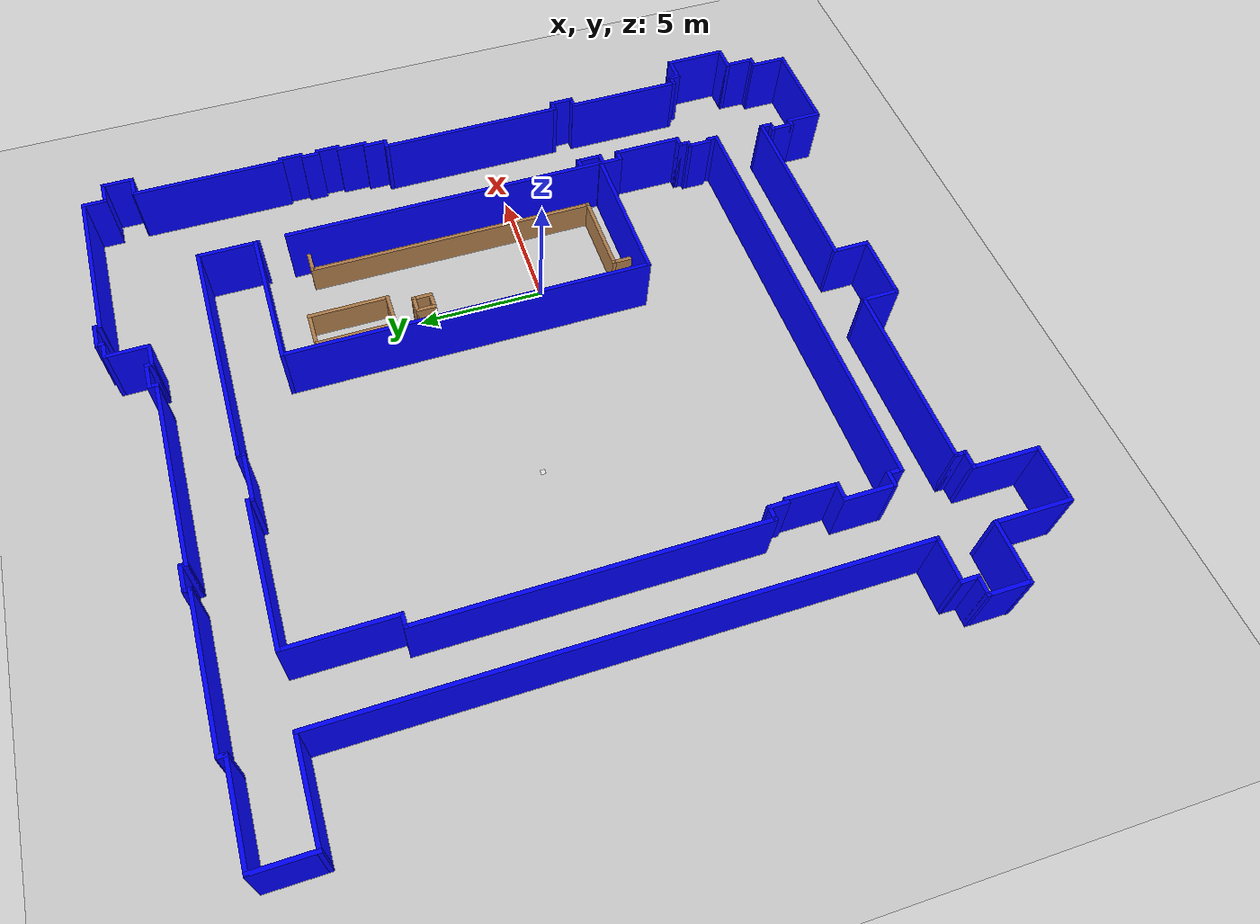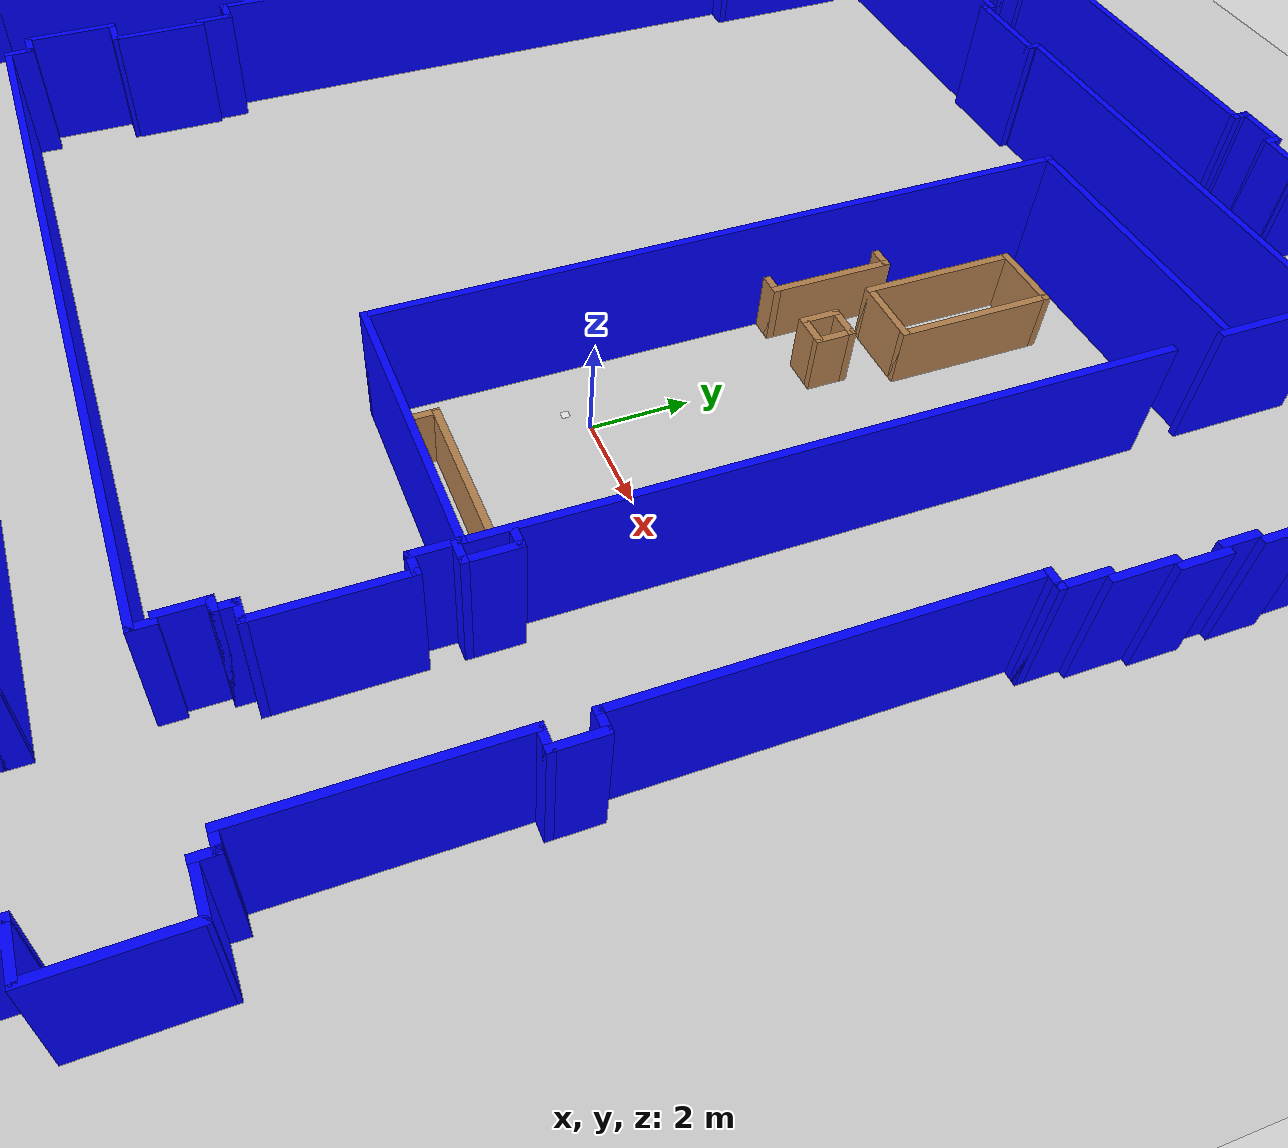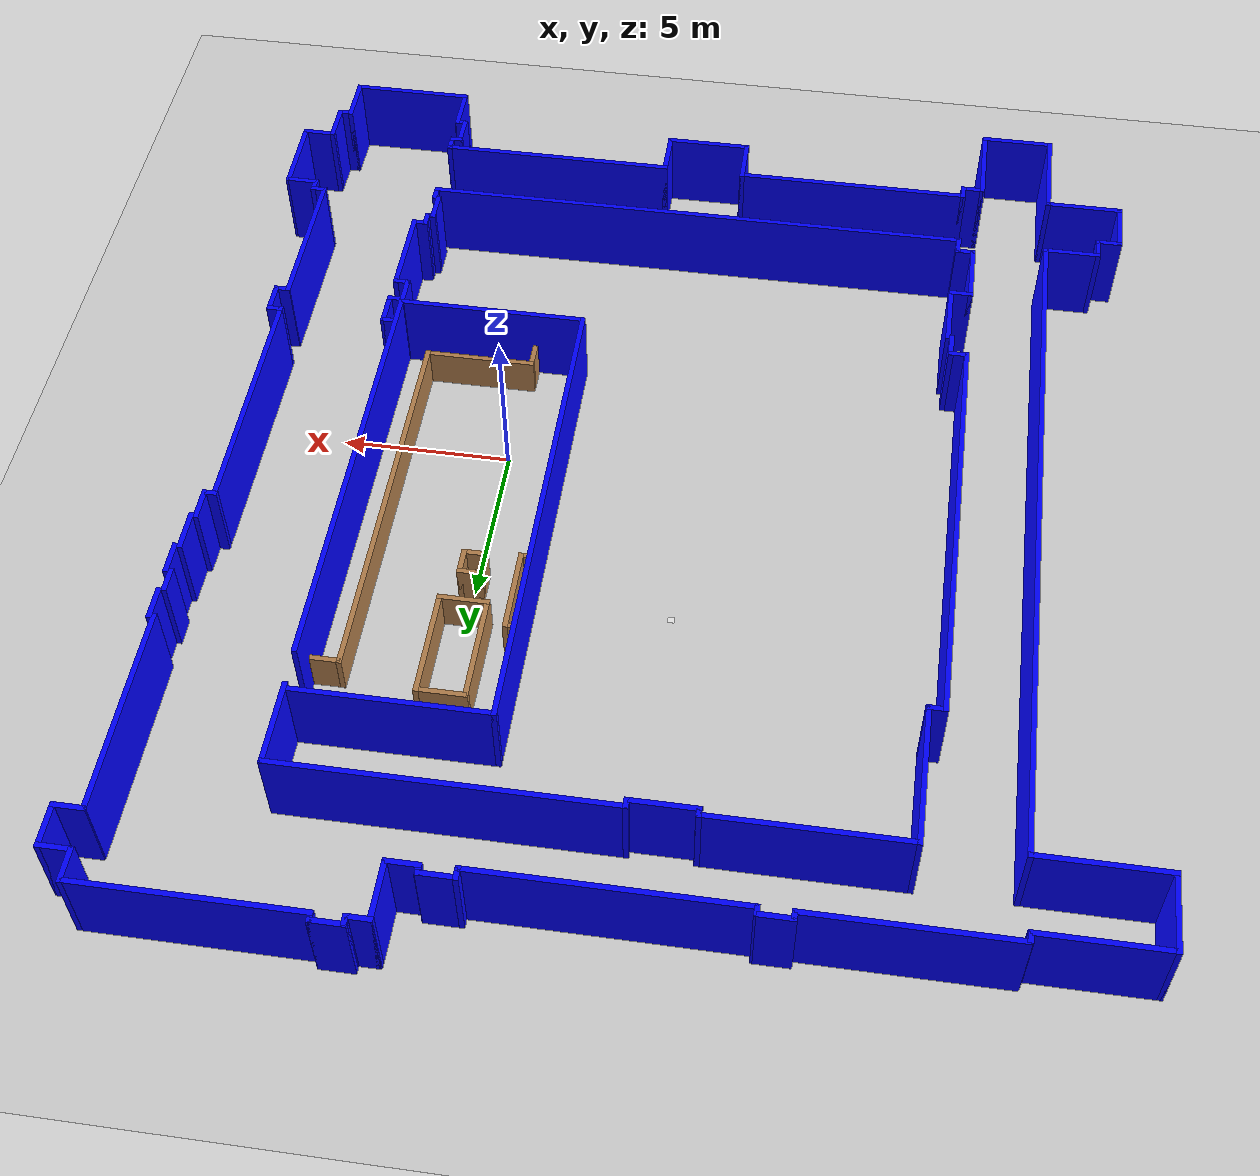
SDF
<sdf version="1.7">
 <world name="a2230_v2">
  <physics type="ode">
   <max_step_size>0.003</max_step_size>
   <real_time_factor>1.0</real_time_factor>
   <real_time_update_rate>1000</real_time_update_rate>
   <gravity>0 0 -9.8</gravity>
  </physics>
  <plugin name="gz::sim::systems::Physics" filename="libgz-sim-physics-system.so"/>
  <plugin name="gz::sim::systems::UserCommands" filename="libgz-sim-user-commands-system.so"/>
  <plugin name="gz::sim::systems::SceneBroadcaster" filename="libgz-sim-scene-broadcaster-system.so"/>
  <plugin name="gz::sim::systems::Sensors" filename="libgz-sim-sensors-system.so">
   <render_engine>ogre2</render_engine>
  </plugin>
  <plugin name="gz::sim::systems::Imu" filename="libgz-sim-imu-system.so"/>
  <scene>
   <ambient>1 1 1 1</ambient>
   <background>0.3 0.7 0.9 1</background>
   <shadows>0</shadows>
   <grid>false</grid>
  </scene>
  <spherical_coordinates>
   <surface_model>EARTH_WGS84</surface_model>
   <world_frame_orientation>ENU</world_frame_orientation>
   <latitude_deg>-22.986687</latitude_deg>
   <longitude_deg>-43.202501</longitude_deg>
   <elevation>0</elevation>
   <heading_deg>0</heading_deg>
  </spherical_coordinates>
  <model name="global_offset_group">
   <pose>-5.19 1.56 0 0 0 0</pose>
   <include><uri>package://mobile_manip/models/my_ground_plane</uri></include>
   <include><uri>package://mobile_manip/models/A2230_arena</uri></include>
   <include>
    <pose>0 0 -5 0 0 0</pose>
    <uri>package://mobile_manip/models/april_tags/Apriltag36_11_00002</uri>
   </include>
  </model>
 </world>
</sdf>

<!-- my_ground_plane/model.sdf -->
<sdf version="1.4">
<model name="my_ground_plane">
  <static>true</static>
    <link name="link">
      <collision name='collision'>
        <geometry>
          <plane>
            <normal>0 0 1</normal>
            <size>150 150</size>
          </plane>
        </geometry>
        <surface>
          <friction>
            <ode>
              <mu>100</mu>
              <mu2>100</mu2>
              <slip1>0.0</slip1>
              <slip2>0.0</slip2>
              <fdir1>0 0 0</fdir1>
            </ode>
          </friction>
          <bounce>
            <restitution_coefficient>0</restitution_coefficient>
            <threshold>1e+06</threshold>
          </bounce>
          <contact>
            <ode>
              <kp>100000000.0</kp>
              <kd>10000.0</kd>
              <max_vel>0.01</max_vel>
              <min_depth>0.0001</min_depth>
            </ode>
          </contact>
        </surface>
        <max_contacts>10</max_contacts>
      </collision>
      <visual name="visual">
        <cast_shadows>false</cast_shadows>
        <geometry>
          <plane>
            <normal>0 0 1</normal>
            <size>40 40</size>
          </plane>
        </geometry>
      </visual>
    </link>
  </model>
</sdf>

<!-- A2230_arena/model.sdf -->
<sdf version='1.6'>
  <model name='A2230_new'>
    <pose frame=''>3.29262 1.5551 0 0 -0 0</pose>
    <link name='Wall_0'>
      <collision name='Wall_0_Collision'>
        <geometry>
          <box>
            <size>16.78 0.15 2.5</size>
          </box>
        </geometry>
        <pose frame=''>0 0 1.25 0 -0 0</pose>
      </collision>
      <visual name='Wall_0_Visual'>
        <pose frame=''>0 0 1.25 0 -0 0</pose>
        <geometry>
          <box>
            <size>16.78 0.15 2.5</size>
          </box>
        </geometry>
            <material>
                <ambient>0.0 0.0 1.0 1</ambient>
                <diffuse>0.0 0.0 1.0 1</diffuse>
                <specular>0.0 0.0 1.0 1</specular>
            </material>
        <meta>
          <layer>0</layer>
        </meta>
      </visual>
      <pose frame=''>0.709394 -10.3929 0 0 -0 0</pose>
    </link>
    <link name='Wall_100'>
      <collision name='Wall_100_Collision'>
        <geometry>
          <box>
            <size>0.367391 0.15 2.5</size>
          </box>
        </geometry>
        <pose frame=''>0 0 1.25 0 -0 0</pose>
      </collision>
      <visual name='Wall_100_Visual'>
        <pose frame=''>0 0 1.25 0 -0 0</pose>
        <geometry>
          <box>
            <size>0.367391 0.15 2.5</size>
          </box>
        </geometry>
            <material>
                <ambient>0.0 0.0 1.0 1</ambient>
                <diffuse>0.0 0.0 1.0 1</diffuse>
                <specular>0.0 0.0 1.0 1</specular>
            </material>
        <meta>
          <layer>0</layer>
        </meta>
      </visual>
      <pose frame=''>5.9153 15.1926 0 0 -0 -1.5708</pose>
    </link>
    <link name='Wall_101'>
      <collision name='Wall_101_Collision'>
        <geometry>
          <box>
            <size>0.75 0.15 2.5</size>
          </box>
        </geometry>
        <pose frame=''>0 0 1.25 0 -0 0</pose>
      </collision>
      <visual name='Wall_101_Visual'>
        <pose frame=''>0 0 1.25 0 -0 0</pose>
        <geometry>
          <box>
            <size>0.75 0.15 2.5</size>
          </box>
        </geometry>
            <material>
                <ambient>0.0 0.0 1.0 1</ambient>
                <diffuse>0.0 0.0 1.0 1</diffuse>
                <specular>0.0 0.0 1.0 1</specular>
            </material>
        <meta>
          <layer>0</layer>
        </meta>
      </visual>
      <pose frame=''>5.6153 15.0839 0 0 -0 3.14159</pose>
    </link>
    <link name='Wall_102'>
      <collision name='Wall_102_Collision'>
        <geometry>
          <box>
            <size>1.75 0.15 2.5</size>
          </box>
        </geometry>
        <pose frame=''>0 0 1.25 0 -0 0</pose>
      </collision>
      <visual name='Wall_102_Visual'>
        <pose frame=''>0 0 1.25 0 -0 0</pose>
        <geometry>
          <box>
            <size>1.75 0.15 2.5</size>
          </box>
        </geometry>
            <material>
                <ambient>0.0 0.0 1.0 1</ambient>
                <diffuse>0.0 0.0 1.0 1</diffuse>
                <specular>0.0 0.0 1.0 1</specular>
            </material>
        <meta>
          <layer>0</layer>
        </meta>
      </visual>
      <pose frame=''>5.3153 14.2839 0 0 -0 -1.5708</pose>
    </link>
    <link name='Wall_103'>
      <collision name='Wall_103_Collision'>
        <geometry>
          <box>
            <size>1 0.15 2.5</size>
          </box>
        </geometry>
        <pose frame=''>0 0 1.25 0 -0 0</pose>
      </collision>
      <visual name='Wall_103_Visual'>
        <pose frame=''>0 0 1.25 0 -0 0</pose>
        <geometry>
          <box>
            <size>1 0.15 2.5</size>
          </box>
        </geometry>
            <material>
                <ambient>0.0 0.0 1.0 1</ambient>
                <diffuse>0.0 0.0 1.0 1</diffuse>
                <specular>0.0 0.0 1.0 1</specular>
            </material>
        <meta>
          <layer>0</layer>
        </meta>
      </visual>
      <pose frame=''>4.8903 13.4839 0 0 -0 3.14159</pose>
    </link>
    <link name='Wall_106'>
      <collision name='Wall_106_Collision'>
        <geometry>
          <box>
            <size>0.35 0.15 2.5</size>
          </box>
        </geometry>
        <pose frame=''>0 0 1.25 0 -0 0</pose>
      </collision>
      <visual name='Wall_106_Visual'>
        <pose frame=''>0 0 1.25 0 -0 0</pose>
        <geometry>
          <box>
            <size>0.35 0.15 2.5</size>
          </box>
        </geometry>
            <material>
                <ambient>0.0 0.0 1.0 1</ambient>
                <diffuse>0.0 0.0 1.0 1</diffuse>
                <specular>0.0 0.0 1.0 1</specular>
            </material>
        <meta>
          <layer>0</layer>
        </meta>
      </visual>
      <pose frame=''>4.4653 13.5839 0 0 -0 1.5708</pose>
    </link>
    <link name='Wall_109'>
      <collision name='Wall_109_Collision'>
        <geometry>
          <box>
            <size>0.402324 0.15 2.5</size>
          </box>
        </geometry>
        <pose frame=''>0 0 1.25 0 -0 0</pose>
      </collision>
      <visual name='Wall_109_Visual'>
        <pose frame=''>0 0 1.25 0 -0 0</pose>
        <geometry>
          <box>
            <size>0.402324 0.15 2.5</size>
          </box>
        </geometry>
            <material>
                <ambient>0.0 0.0 1.0 1</ambient>
                <diffuse>0.0 0.0 1.0 1</diffuse>
                <specular>0.0 0.0 1.0 1</specular>
            </material>
        <meta>
          <layer>0</layer>
        </meta>
      </visual>
      <pose frame=''>3.5066 13.5665 0 0 -0 1.5708</pose>
    </link>
    <link name='Wall_110'>
      <collision name='Wall_110_Collision'>
        <geometry>
          <box>
            <size>1.09783 0.15 2.5</size>
          </box>
        </geometry>
        <pose frame=''>0 0 1.25 0 -0 0</pose>
      </collision>
      <visual name='Wall_110_Visual'>
        <pose frame=''>0 0 1.25 0 -0 0</pose>
        <geometry>
          <box>
            <size>1.09783 0.15 2.5</size>
          </box>
        </geometry>
            <material>
                <ambient>0.0 0.0 1.0 1</ambient>
                <diffuse>0.0 0.0 1.0 1</diffuse>
                <specular>0.0 0.0 1.0 1</specular>
            </material>
        <meta>
          <layer>0</layer>
        </meta>
      </visual>
      <pose frame=''>3.98052 13.6926 0 0 -0 0</pose>
    </link>
    <link name='Wall_112'>
      <collision name='Wall_112_Collision'>
        <geometry>
          <box>
            <size>1 0.15 2.5</size>
          </box>
        </geometry>
        <pose frame=''>0 0 1.25 0 -0 0</pose>
      </collision>
      <visual name='Wall_112_Visual'>
        <pose frame=''>0 0 1.25 0 -0 0</pose>
        <geometry>
          <box>
            <size>1 0.15 2.5</size>
          </box>
        </geometry>
            <material>
                <ambient>0.0 0.0 1.0 1</ambient>
                <diffuse>0.0 0.0 1.0 1</diffuse>
                <specular>0.0 0.0 1.0 1</specular>
            </material>
        <meta>
          <layer>0</layer>
        </meta>
      </visual>
      <pose frame=''>6.3403 15.3013 0 0 -0 0</pose>
    </link>
    <link name='Wall_113'>
      <collision name='Wall_113_Collision'>
        <geometry>
          <box>
            <size>0.32 0.15 2.5</size>
          </box>
        </geometry>
        <pose frame=''>0 0 1.25 0 -0 0</pose>
      </collision>
      <visual name='Wall_113_Visual'>
        <pose frame=''>0 0 1.25 0 -0 0</pose>
        <geometry>
          <box>
            <size>0.32 0.15 2.5</size>
          </box>
        </geometry>
            <material>
                <ambient>0.0 0.0 1.0 1</ambient>
                <diffuse>0.0 0.0 1.0 1</diffuse>
                <specular>0.0 0.0 1.0 1</specular>
            </material>
        <meta>
          <layer>0</layer>
        </meta>
      </visual>
      <pose frame=''>6.7653 15.2163 0 0 -0 -1.5708</pose>
    </link>
    <link name='Wall_115'>
      <collision name='Wall_115_Collision'>
        <geometry>
          <box>
            <size>6.4 0.15 2.5</size>
          </box>
        </geometry>
        <pose frame=''>0 0 1.25 0 -0 0</pose>
      </collision>
      <visual name='Wall_115_Visual'>
        <pose frame=''>0 0 1.25 0 -0 0</pose>
        <geometry>
          <box>
            <size>6.4 0.15 2.5</size>
          </box>
        </geometry>
            <material>
                <ambient>0.0 0.0 1.0 1</ambient>
                <diffuse>0.0 0.0 1.0 1</diffuse>
                <specular>0.0 0.0 1.0 1</specular>
            </material>
        <meta>
          <layer>0</layer>
        </meta>
      </visual>
      <pose frame=''>9.90334 15.11 0 0 -0 3.14159</pose>
    </link>
    <link name='Wall_117'>
      <collision name='Wall_117_Collision'>
        <geometry>
          <box>
            <size>1 0.15 2.5</size>
          </box>
        </geometry>
        <pose frame=''>0 0 1.25 0 -0 0</pose>
      </collision>
      <visual name='Wall_117_Visual'>
        <pose frame=''>0 0 1.25 0 -0 0</pose>
        <geometry>
          <box>
            <size>1 0.15 2.5</size>
          </box>
        </geometry>
            <material>
                <ambient>0.0 0.0 1.0 1</ambient>
                <diffuse>0.0 0.0 1.0 1</diffuse>
                <specular>0.0 0.0 1.0 1</specular>
            </material>
        <meta>
          <layer>0</layer>
        </meta>
      </visual>
      <pose frame=''>13.0283 14.685 0 0 -0 -1.5708</pose>
    </link>
    <link name='Wall_118'>
      <collision name='Wall_118_Collision'>
        <geometry>
          <box>
            <size>1 0.15 2.5</size>
          </box>
        </geometry>
        <pose frame=''>0 0 1.25 0 -0 0</pose>
      </collision>
      <visual name='Wall_118_Visual'>
        <pose frame=''>0 0 1.25 0 -0 0</pose>
        <geometry>
          <box>
            <size>1 0.15 2.5</size>
          </box>
        </geometry>
            <material>
                <ambient>0.0 0.0 1.0 1</ambient>
                <diffuse>0.0 0.0 1.0 1</diffuse>
                <specular>0.0 0.0 1.0 1</specular>
            </material>
        <meta>
          <layer>0</layer>
        </meta>
      </visual>
      <pose frame=''>13.4533 14.26 0 0 -0 0</pose>
    </link>
    <link name='Wall_119'>
      <collision name='Wall_119_Collision'>
        <geometry>
          <box>
            <size>1.3 0.15 2.5</size>
          </box>
        </geometry>
        <pose frame=''>0 0 1.25 0 -0 0</pose>
      </collision>
      <visual name='Wall_119_Visual'>
        <pose frame=''>0 0 1.25 0 -0 0</pose>
        <geometry>
          <box>
            <size>1.3 0.15 2.5</size>
          </box>
        </geometry>
            <material>
                <ambient>0.0 0.0 1.0 1</ambient>
                <diffuse>0.0 0.0 1.0 1</diffuse>
                <specular>0.0 0.0 1.0 1</specular>
            </material>
        <meta>
          <layer>0</layer>
        </meta>
      </visual>
      <pose frame=''>13.8783 13.685 0 0 -0 -1.5708</pose>
    </link>
    <link name='Wall_121'>
      <collision name='Wall_121_Collision'>
        <geometry>
          <box>
            <size>0.943 0.15 2.5</size>
          </box>
        </geometry>
        <pose frame=''>0 0 1.25 0 -0 0</pose>
      </collision>
      <visual name='Wall_121_Visual'>
        <pose frame=''>0 0 1.25 0 -0 0</pose>
        <geometry>
          <box>
            <size>0.943 0.15 2.5</size>
          </box>
        </geometry>
            <material>
                <ambient>0.0 0.0 1.0 1</ambient>
                <diffuse>0.0 0.0 1.0 1</diffuse>
                <specular>0.0 0.0 1.0 1</specular>
            </material>
        <meta>
          <layer>0</layer>
        </meta>
      </visual>
      <pose frame=''>13.4818 13.11 0 0 -0 3.14159</pose>
    </link>
    <link name='Wall_123'>
      <collision name='Wall_123_Collision'>
        <geometry>
          <box>
            <size>7.5 0.15 2.5</size>
          </box>
        </geometry>
        <pose frame=''>0 0 1.25 0 -0 0</pose>
      </collision>
      <visual name='Wall_123_Visual'>
        <pose frame=''>0 0 1.25 0 -0 0</pose>
        <geometry>
          <box>
            <size>7.5 0.15 2.5</size>
          </box>
        </geometry>
            <material>
                <ambient>0.0 0.0 1.0 1</ambient>
                <diffuse>0.0 0.0 1.0 1</diffuse>
                <specular>0.0 0.0 1.0 1</specular>
            </material>
        <meta>
          <layer>0</layer>
        </meta>
      </visual>
      <pose frame=''>-0.168398 13.4405 0 0 -0 3.14159</pose>
    </link>
    <link name='Wall_124'>
      <collision name='Wall_124_Collision'>
        <geometry>
          <box>
            <size>0.33 0.15 2.5</size>
          </box>
        </geometry>
        <pose frame=''>0 0 1.25 0 -0 0</pose>
      </collision>
      <visual name='Wall_124_Visual'>
        <pose frame=''>0 0 1.25 0 -0 0</pose>
        <geometry>
          <box>
            <size>0.33 0.15 2.5</size>
          </box>
        </geometry>
            <material>
                <ambient>0.0 0.0 1.0 1</ambient>
                <diffuse>0.0 0.0 1.0 1</diffuse>
                <specular>0.0 0.0 1.0 1</specular>
            </material>
        <meta>
          <layer>0</layer>
        </meta>
      </visual>
      <pose frame=''>-3.8434 13.5305 0 0 -0 1.5708</pose>
    </link>
    <link name='Wall_127'>
      <collision name='Wall_127_Collision'>
        <geometry>
          <box>
            <size>5.75 0.15 2.5</size>
          </box>
        </geometry>
        <pose frame=''>0 0 1.25 0 -0 0</pose>
      </collision>
      <visual name='Wall_127_Visual'>
        <pose frame=''>0 0 1.25 0 -0 0</pose>
        <geometry>
          <box>
            <size>5.75 0.15 2.5</size>
          </box>
        </geometry>
            <material>
                <ambient>0.0 0.0 1.0 1</ambient>
                <diffuse>0.0 0.0 1.0 1</diffuse>
                <specular>0.0 0.0 1.0 1</specular>
            </material>
        <meta>
          <layer>0</layer>
        </meta>
      </visual>
      <pose frame=''>-7.55427 13.4405 0 0 -0 0</pose>
    </link>
    <link name='Wall_128'>
      <collision name='Wall_128_Collision'>
        <geometry>
          <box>
            <size>0.341304 0.15 2.5</size>
          </box>
        </geometry>
        <pose frame=''>0 0 1.25 0 -0 0</pose>
      </collision>
      <visual name='Wall_128_Visual'>
        <pose frame=''>0 0 1.25 0 -0 0</pose>
        <geometry>
          <box>
            <size>0.341304 0.15 2.5</size>
          </box>
        </geometry>
            <material>
                <ambient>0.0 0.0 1.0 1</ambient>
                <diffuse>0.0 0.0 1.0 1</diffuse>
                <specular>0.0 0.0 1.0 1</specular>
            </material>
        <meta>
          <layer>0</layer>
        </meta>
      </visual>
      <pose frame=''>-4.75427 13.5361 0 0 -0 1.5708</pose>
    </link>
    <link name='Wall_129'>
      <collision name='Wall_129_Collision'>
        <geometry>
          <box>
            <size>1 0.15 2.5</size>
          </box>
        </geometry>
        <pose frame=''>0 0 1.25 0 -0 0</pose>
      </collision>
      <visual name='Wall_129_Visual'>
        <pose frame=''>0 0 1.25 0 -0 0</pose>
        <geometry>
          <box>
            <size>1 0.15 2.5</size>
          </box>
        </geometry>
            <material>
                <ambient>0.0 0.0 1.0 1</ambient>
                <diffuse>0.0 0.0 1.0 1</diffuse>
                <specular>0.0 0.0 1.0 1</specular>
            </material>
        <meta>
          <layer>0</layer>
        </meta>
      </visual>
      <pose frame=''>-4.32927 13.6318 0 0 -0 0</pose>
    </link>
    <link name='Wall_13'>
      <collision name='Wall_13_Collision'>
        <geometry>
          <box>
            <size>5.65 0.15 2.5</size>
          </box>
        </geometry>
        <pose frame=''>0 0 1.25 0 -0 0</pose>
      </collision>
      <visual name='Wall_13_Visual'>
        <pose frame=''>0 0 1.25 0 -0 0</pose>
        <geometry>
          <box>
            <size>5.65 0.15 2.5</size>
          </box>
        </geometry>
            <material>
                <ambient>0.0 0.0 1.0 1</ambient>
                <diffuse>0.0 0.0 1.0 1</diffuse>
                <specular>0.0 0.0 1.0 1</specular>
            </material>
        <meta>
          <layer>0</layer>
        </meta>
      </visual>
      <pose frame=''>-4.87627 11.1295 0 0 -0 0</pose>
    </link>
    <link name='Wall_132'>
      <collision name='Wall_132_Collision'>
        <geometry>
          <box>
            <size>21.577 0.15 2.5</size>
          </box>
        </geometry>
        <pose frame=''>0 0 1.25 0 -0 0</pose>
      </collision>
      <visual name='Wall_132_Visual'>
        <pose frame=''>0 0 1.25 0 -0 0</pose>
        <geometry>
          <box>
            <size>21.577 0.15 2.5</size>
          </box>
        </geometry>
            <material>
                <ambient>0.0 0.0 1.0 1</ambient>
                <diffuse>0.0 0.0 1.0 1</diffuse>
                <specular>0.0 0.0 1.0 1</specular>
            </material>
        <meta>
          <layer>0</layer>
        </meta>
      </visual>
      <pose frame=''>-10.3216 0.385397 0 0 -0 1.5708</pose>
    </link>
    <link name='Wall_134'>
      <collision name='Wall_134_Collision'>
        <geometry>
          <box>
            <size>2.25 0.15 2.5</size>
          </box>
        </geometry>
        <pose frame=''>0 0 1.25 0 -0 0</pose>
      </collision>
      <visual name='Wall_134_Visual'>
        <pose frame=''>0 0 1.25 0 -0 0</pose>
        <geometry>
          <box>
            <size>2.25 0.15 2.5</size>
          </box>
        </geometry>
            <material>
                <ambient>0.0 0.0 1.0 1</ambient>
                <diffuse>0.0 0.0 1.0 1</diffuse>
                <specular>0.0 0.0 1.0 1</specular>
            </material>
        <meta>
          <layer>0</layer>
        </meta>
      </visual>
      <pose frame=''>-13.8783 12.1457 0 0 -0 1.5708</pose>
    </link>
    <link name='Wall_135'>
      <collision name='Wall_135_Collision'>
        <geometry>
          <box>
            <size>3.65 0.15 2.5</size>
          </box>
        </geometry>
        <pose frame=''>0 0 1.25 0 -0 0</pose>
      </collision>
      <visual name='Wall_135_Visual'>
        <pose frame=''>0 0 1.25 0 -0 0</pose>
        <geometry>
          <box>
            <size>3.65 0.15 2.5</size>
          </box>
        </geometry>
            <material>
                <ambient>0.0 0.0 1.0 1</ambient>
                <diffuse>0.0 0.0 1.0 1</diffuse>
                <specular>0.0 0.0 1.0 1</specular>
            </material>
        <meta>
          <layer>0</layer>
        </meta>
      </visual>
      <pose frame=''>-12.1283 13.1957 0 0 -0 0</pose>
    </link>
    <link name='Wall_138'>
      <collision name='Wall_138_Collision'>
        <geometry>
          <box>
            <size>0.35 0.15 2.5</size>
          </box>
        </geometry>
        <pose frame=''>0 0 1.25 0 -0 0</pose>
      </collision>
      <visual name='Wall_138_Visual'>
        <pose frame=''>0 0 1.25 0 -0 0</pose>
        <geometry>
          <box>
            <size>0.35 0.15 2.5</size>
          </box>
        </geometry>
            <material>
                <ambient>0.0 0.0 1.0 1</ambient>
                <diffuse>0.0 0.0 1.0 1</diffuse>
                <specular>0.0 0.0 1.0 1</specular>
            </material>
        <meta>
          <layer>0</layer>
        </meta>
      </visual>
      <pose frame=''>-10.3783 13.2957 0 0 -0 1.5708</pose>
    </link>
    <link name='Wall_141'>
      <collision name='Wall_141_Collision'>
        <geometry>
          <box>
            <size>0.3 0.15 2.5</size>
          </box>
        </geometry>
        <pose frame=''>0 0 1.25 0 -0 0</pose>
      </collision>
      <visual name='Wall_141_Visual'>
        <pose frame=''>0 0 1.25 0 -0 0</pose>
        <geometry>
          <box>
            <size>0.3 0.15 2.5</size>
          </box>
        </geometry>
            <material>
                <ambient>0.0 0.0 1.0 1</ambient>
                <diffuse>0.0 0.0 1.0 1</diffuse>
                <specular>0.0 0.0 1.0 1</specular>
            </material>
        <meta>
          <layer>0</layer>
        </meta>
      </visual>
      <pose frame=''>-2.12627 11.0545 0 0 -0 -1.5708</pose>
    </link>
    <link name='Wall_145'>
      <collision name='Wall_145_Collision'>
        <geometry>
          <box>
            <size>1.99 0.15 2.5</size>
          </box>
        </geometry>
        <pose frame=''>0 0 1.25 0 -0 0</pose>
      </collision>
      <visual name='Wall_145_Visual'>
        <pose frame=''>0 0 1.25 0 -0 0</pose>
        <geometry>
          <box>
            <size>1.99 0.15 2.5</size>
          </box>
        </geometry>
            <material>
                <ambient>0.0 0.0 1.0 1</ambient>
                <diffuse>0.0 0.0 1.0 1</diffuse>
                <specular>0.0 0.0 1.0 1</specular>
            </material>
        <meta>
          <layer>0</layer>
        </meta>
      </visual>
      <pose frame=''>-1.20921 10.9612 0 0 -0 3.14159</pose>
    </link>
    <link name='Wall_147'>
      <collision name='Wall_147_Collision'>
        <geometry>
          <box>
            <size>0.334 0.15 2.5</size>
          </box>
        </geometry>
        <pose frame=''>0 0 1.25 0 -0 0</pose>
      </collision>
      <visual name='Wall_147_Visual'>
        <pose frame=''>0 0 1.25 0 -0 0</pose>
        <geometry>
          <box>
            <size>0.334 0.15 2.5</size>
          </box>
        </geometry>
            <material>
                <ambient>0.0 0.0 1.0 1</ambient>
                <diffuse>0.0 0.0 1.0 1</diffuse>
                <specular>0.0 0.0 1.0 1</specular>
            </material>
        <meta>
          <layer>0</layer>
        </meta>
      </visual>
      <pose frame=''>-0.289215 11.0532 0 0 -0 1.5708</pose>
    </link>
    <link name='Wall_149'>
      <collision name='Wall_149_Collision'>
        <geometry>
          <box>
            <size>0.6 0.15 2.5</size>
          </box>
        </geometry>
        <pose frame=''>0 0 1.25 0 -0 0</pose>
      </collision>
      <visual name='Wall_149_Visual'>
        <pose frame=''>0 0 1.25 0 -0 0</pose>
        <geometry>
          <box>
            <size>0.6 0.15 2.5</size>
          </box>
        </geometry>
            <material>
                <ambient>0.0 0.0 1.0 1</ambient>
                <diffuse>0.0 0.0 1.0 1</diffuse>
                <specular>0.0 0.0 1.0 1</specular>
            </material>
        <meta>
          <layer>0</layer>
        </meta>
      </visual>
      <pose frame=''>-7.84377 7.13786 0 0 -0 0</pose>
    </link>
    <link name='Wall_15'>
      <collision name='Wall_15_Collision'>
        <geometry>
          <box>
            <size>9.45 0.15 2.5</size>
          </box>
        </geometry>
        <pose frame=''>0 0 1.25 0 -0 0</pose>
      </collision>
      <visual name='Wall_15_Visual'>
        <pose frame=''>0 0 1.25 0 -0 0</pose>
        <geometry>
          <box>
            <size>9.45 0.15 2.5</size>
          </box>
        </geometry>
            <material>
                <ambient>0.0 0.0 1.0 1</ambient>
                <diffuse>0.0 0.0 1.0 1</diffuse>
                <specular>0.0 0.0 1.0 1</specular>
            </material>
        <meta>
          <layer>0</layer>
        </meta>
      </visual>
      <pose frame=''>4.40541 11.1419 0 0 -0 0</pose>
    </link>
    <link name='Wall_151'>
      <collision name='Wall_151_Collision'>
        <geometry>
          <box>
            <size>0.619 0.15 2.5</size>
          </box>
        </geometry>
        <pose frame=''>0 0 1.25 0 -0 0</pose>
      </collision>
      <visual name='Wall_151_Visual'>
        <pose frame=''>0 0 1.25 0 -0 0</pose>
        <geometry>
          <box>
            <size>0.619 0.15 2.5</size>
          </box>
        </geometry>
            <material>
                <ambient>0.0 0.0 1.0 1</ambient>
                <diffuse>0.0 0.0 1.0 1</diffuse>
                <specular>0.0 0.0 1.0 1</specular>
            </material>
        <meta>
          <layer>0</layer>
        </meta>
      </visual>
      <pose frame=''>-7.8475 -9.91068 0 0 -0 0</pose>
    </link>
    <link name='Wall_154'>
      <collision name='Wall_154_Collision'>
        <geometry>
          <box>
            <size>0.63 0.15 2.5</size>
          </box>
        </geometry>
        <pose frame=''>0 0 1.25 0 -0 0</pose>
      </collision>
      <visual name='Wall_154_Visual'>
        <pose frame=''>0 0 1.25 0 -0 0</pose>
        <geometry>
          <box>
            <size>0.63 0.15 2.5</size>
          </box>
        </geometry>
            <material>
                <ambient>0.0 0.0 1.0 1</ambient>
                <diffuse>0.0 0.0 1.0 1</diffuse>
                <specular>0.0 0.0 1.0 1</specular>
            </material>
        <meta>
          <layer>0</layer>
        </meta>
      </visual>
      <pose frame=''>-7.61299 -10.1507 0 0 -0 -1.5708</pose>
    </link>
    <link name='Wall_156'>
      <collision name='Wall_156_Collision'>
        <geometry>
          <box>
            <size>0.738 0.15 2.5</size>
          </box>
        </geometry>
        <pose frame=''>0 0 1.25 0 -0 0</pose>
      </collision>
      <visual name='Wall_156_Visual'>
        <pose frame=''>0 0 1.25 0 -0 0</pose>
        <geometry>
          <box>
            <size>0.738 0.15 2.5</size>
          </box>
        </geometry>
            <material>
                <ambient>0.0 0.0 1.0 1</ambient>
                <diffuse>0.0 0.0 1.0 1</diffuse>
                <specular>0.0 0.0 1.0 1</specular>
            </material>
        <meta>
          <layer>0</layer>
        </meta>
      </visual>
      <pose frame=''>-7.78799 -8.06068 0 0 -0 0</pose>
    </link>
    <link name='Wall_159'>
      <collision name='Wall_159_Collision'>
        <geometry>
          <box>
            <size>0.811382 0.15 2.5</size>
          </box>
        </geometry>
        <pose frame=''>0 0 1.25 0 -0 0</pose>
      </collision>
      <visual name='Wall_159_Visual'>
        <pose frame=''>0 0 1.25 0 -0 0</pose>
        <geometry>
          <box>
            <size>0.811382 0.15 2.5</size>
          </box>
        </geometry>
            <material>
                <ambient>0.0 0.0 1.0 1</ambient>
                <diffuse>0.0 0.0 1.0 1</diffuse>
                <specular>0.0 0.0 1.0 1</specular>
            </material>
        <meta>
          <layer>0</layer>
        </meta>
      </visual>
      <pose frame=''>-7.59855 -5.83255 0 0 -0 -1.5708</pose>
    </link>
    <link name='Wall_161'>
      <collision name='Wall_161_Collision'>
        <geometry>
          <box>
            <size>0.59 0.15 2.5</size>
          </box>
        </geometry>
        <pose frame=''>0 0 1.25 0 -0 0</pose>
      </collision>
      <visual name='Wall_161_Visual'>
        <pose frame=''>0 0 1.25 0 -0 0</pose>
        <geometry>
          <box>
            <size>0.59 0.15 2.5</size>
          </box>
        </geometry>
            <material>
                <ambient>0.0 0.0 1.0 1</ambient>
                <diffuse>0.0 0.0 1.0 1</diffuse>
                <specular>0.0 0.0 1.0 1</specular>
            </material>
        <meta>
          <layer>0</layer>
        </meta>
      </visual>
      <pose frame=''>-7.81855 -5.50193 0 0 -0 3.14159</pose>
    </link>
    <link name='Wall_163'>
      <collision name='Wall_163_Collision'>
        <geometry>
          <box>
            <size>0.75 0.15 2.5</size>
          </box>
        </geometry>
        <pose frame=''>0 0 1.25 0 -0 0</pose>
      </collision>
      <visual name='Wall_163_Visual'>
        <pose frame=''>0 0 1.25 0 -0 0</pose>
        <geometry>
          <box>
            <size>0.75 0.15 2.5</size>
          </box>
        </geometry>
            <material>
                <ambient>0.0 0.0 1.0 1</ambient>
                <diffuse>0.0 0.0 1.0 1</diffuse>
                <specular>0.0 0.0 1.0 1</specular>
            </material>
        <meta>
          <layer>0</layer>
        </meta>
      </visual>
      <pose frame=''>-11.9396 -10.6282 0 0 -0 -1.5708</pose>
    </link>
    <link name='Wall_164'>
      <collision name='Wall_164_Collision'>
        <geometry>
          <box>
            <size>0.812 0.15 2.5</size>
          </box>
        </geometry>
        <pose frame=''>0 0 1.25 0 -0 0</pose>
      </collision>
      <visual name='Wall_164_Visual'>
        <pose frame=''>0 0 1.25 0 -0 0</pose>
        <geometry>
          <box>
            <size>0.812 0.15 2.5</size>
          </box>
        </geometry>
            <material>
                <ambient>0.0 0.0 1.0 1</ambient>
                <diffuse>0.0 0.0 1.0 1</diffuse>
                <specular>0.0 0.0 1.0 1</specular>
            </material>
        <meta>
          <layer>0</layer>
        </meta>
      </visual>
      <pose frame=''>-12.2706 -10.9282 0 0 -0 3.14159</pose>
    </link>
    <link name='Wall_167'>
      <collision name='Wall_167_Collision'>
        <geometry>
          <box>
            <size>1.662 0.15 2.5</size>
          </box>
        </geometry>
        <pose frame=''>0 0 1.25 0 -0 0</pose>
      </collision>
      <visual name='Wall_167_Visual'>
        <pose frame=''>0 0 1.25 0 -0 0</pose>
        <geometry>
          <box>
            <size>1.662 0.15 2.5</size>
          </box>
        </geometry>
            <material>
                <ambient>0.0 0.0 1.0 1</ambient>
                <diffuse>0.0 0.0 1.0 1</diffuse>
                <specular>0.0 0.0 1.0 1</specular>
            </material>
        <meta>
          <layer>0</layer>
        </meta>
      </visual>
      <pose frame=''>-12.6016 -11.6842 0 0 -0 -1.5708</pose>
    </link>
    <link name='Wall_169'>
      <collision name='Wall_169_Collision'>
        <geometry>
          <box>
            <size>0.5 0.15 2.5</size>
          </box>
        </geometry>
        <pose frame=''>0 0 1.25 0 -0 0</pose>
      </collision>
      <visual name='Wall_169_Visual'>
        <pose frame=''>0 0 1.25 0 -0 0</pose>
        <geometry>
          <box>
            <size>0.5 0.15 2.5</size>
          </box>
        </geometry>
            <material>
                <ambient>0.0 0.0 1.0 1</ambient>
                <diffuse>0.0 0.0 1.0 1</diffuse>
                <specular>0.0 0.0 1.0 1</specular>
            </material>
        <meta>
          <layer>0</layer>
        </meta>
      </visual>
      <pose frame=''>9.25504 -8.81578 0 0 -0 3.14159</pose>
    </link>
    <link name='Wall_17'>
      <collision name='Wall_17_Collision'>
        <geometry>
          <box>
            <size>2.5 0.15 2.5</size>
          </box>
        </geometry>
        <pose frame=''>0 0 1.25 0 -0 0</pose>
      </collision>
      <visual name='Wall_17_Visual'>
        <pose frame=''>0 0 1.25 0 -0 0</pose>
        <geometry>
          <box>
            <size>2.5 0.15 2.5</size>
          </box>
        </geometry>
            <material>
                <ambient>0.0 0.0 1.0 1</ambient>
                <diffuse>0.0 0.0 1.0 1</diffuse>
                <specular>0.0 0.0 1.0 1</specular>
            </material>
        <meta>
          <layer>0</layer>
        </meta>
      </visual>
      <pose frame=''>9.05541 9.96689 0 0 -0 -1.5708</pose>
    </link>
    <link name='Wall_170'>
      <collision name='Wall_170_Collision'>
        <geometry>
          <box>
            <size>0.5 0.15 2.5</size>
          </box>
        </geometry>
        <pose frame=''>0 0 1.25 0 -0 0</pose>
      </collision>
      <visual name='Wall_170_Visual'>
        <pose frame=''>0 0 1.25 0 -0 0</pose>
        <geometry>
          <box>
            <size>0.5 0.15 2.5</size>
          </box>
        </geometry>
            <material>
                <ambient>0.0 0.0 1.0 1</ambient>
                <diffuse>0.0 0.0 1.0 1</diffuse>
                <specular>0.0 0.0 1.0 1</specular>
            </material>
        <meta>
          <layer>0</layer>
        </meta>
      </visual>
      <pose frame=''>9.08004 -8.99078 0 0 -0 -1.5708</pose>
    </link>
    <link name='Wall_171'>
      <collision name='Wall_171_Collision'>
        <geometry>
          <box>
            <size>0.331 0.15 2.5</size>
          </box>
        </geometry>
        <pose frame=''>0 0 1.25 0 -0 0</pose>
      </collision>
      <visual name='Wall_171_Visual'>
        <pose frame=''>0 0 1.25 0 -0 0</pose>
        <geometry>
          <box>
            <size>0.331 0.15 2.5</size>
          </box>
        </geometry>
            <material>
                <ambient>0.0 0.0 1.0 1</ambient>
                <diffuse>0.0 0.0 1.0 1</diffuse>
                <specular>0.0 0.0 1.0 1</specular>
            </material>
        <meta>
          <layer>0</layer>
        </meta>
      </visual>
      <pose frame=''>8.98954 -9.16578 0 0 -0 3.14159</pose>
    </link>
    <link name='Wall_173'>
      <collision name='Wall_173_Collision'>
        <geometry>
          <box>
            <size>0.5 0.15 2.5</size>
          </box>
        </geometry>
        <pose frame=''>0 0 1.25 0 -0 0</pose>
      </collision>
      <visual name='Wall_173_Visual'>
        <pose frame=''>0 0 1.25 0 -0 0</pose>
        <geometry>
          <box>
            <size>0.5 0.15 2.5</size>
          </box>
        </geometry>
            <material>
                <ambient>0.0 0.0 1.0 1</ambient>
                <diffuse>0.0 0.0 1.0 1</diffuse>
                <specular>0.0 0.0 1.0 1</specular>
            </material>
        <meta>
          <layer>0</layer>
        </meta>
      </visual>
      <pose frame=''>9.0244 -10.2179 0 0 -0 1.5708</pose>
    </link>
    <link name='Wall_177'>
      <collision name='Wall_177_Collision'>
        <geometry>
          <box>
            <size>0.973 0.15 2.5</size>
          </box>
        </geometry>
        <pose frame=''>0 0 1.25 0 -0 0</pose>
      </collision>
      <visual name='Wall_177_Visual'>
        <pose frame=''>0 0 1.25 0 -0 0</pose>
        <geometry>
          <box>
            <size>0.973 0.15 2.5</size>
          </box>
        </geometry>
            <material>
                <ambient>0.0 0.0 1.0 1</ambient>
                <diffuse>0.0 0.0 1.0 1</diffuse>
                <specular>0.0 0.0 1.0 1</specular>
            </material>
        <meta>
          <layer>0</layer>
        </meta>
      </visual>
      <pose frame=''>8.90416 -9.58684 0 0 -0 1.5708</pose>
    </link>
    <link name='Wall_179'>
      <collision name='Wall_179_Collision'>
        <geometry>
          <box>
            <size>0.5 0.15 2.5</size>
          </box>
        </geometry>
        <pose frame=''>0 0 1.25 0 -0 0</pose>
      </collision>
      <visual name='Wall_179_Visual'>
        <pose frame=''>0 0 1.25 0 -0 0</pose>
        <geometry>
          <box>
            <size>0.5 0.15 2.5</size>
          </box>
        </geometry>
            <material>
                <ambient>0.0 0.0 1.0 1</ambient>
                <diffuse>0.0 0.0 1.0 1</diffuse>
                <specular>0.0 0.0 1.0 1</specular>
            </material>
        <meta>
          <layer>0</layer>
        </meta>
      </visual>
      <pose frame=''>12.7915 -9.87883 0 0 -0 0</pose>
    </link>
    <link name='Wall_180'>
      <collision name='Wall_180_Collision'>
        <geometry>
          <box>
            <size>0.48 0.15 2.5</size>
          </box>
        </geometry>
        <pose frame=''>0 0 1.25 0 -0 0</pose>
      </collision>
      <visual name='Wall_180_Visual'>
        <pose frame=''>0 0 1.25 0 -0 0</pose>
        <geometry>
          <box>
            <size>0.48 0.15 2.5</size>
          </box>
        </geometry>
            <material>
                <ambient>0.0 0.0 1.0 1</ambient>
                <diffuse>0.0 0.0 1.0 1</diffuse>
                <specular>0.0 0.0 1.0 1</specular>
            </material>
        <meta>
          <layer>0</layer>
        </meta>
      </visual>
      <pose frame=''>12.9665 -10.0438 0 0 -0 -1.5708</pose>
    </link>
    <link name='Wall_182'>
      <collision name='Wall_182_Collision'>
        <geometry>
          <box>
            <size>0.5 0.15 2.5</size>
          </box>
        </geometry>
        <pose frame=''>0 0 1.25 0 -0 0</pose>
      </collision>
      <visual name='Wall_182_Visual'>
        <pose frame=''>0 0 1.25 0 -0 0</pose>
        <geometry>
          <box>
            <size>0.5 0.15 2.5</size>
          </box>
        </geometry>
            <material>
                <ambient>0.0 0.0 1.0 1</ambient>
                <diffuse>0.0 0.0 1.0 1</diffuse>
                <specular>0.0 0.0 1.0 1</specular>
            </material>
        <meta>
          <layer>0</layer>
        </meta>
      </visual>
      <pose frame=''>12.8116 -4.4884 0 0 -0 0</pose>
    </link>
    <link name='Wall_183'>
      <collision name='Wall_183_Collision'>
        <geometry>
          <box>
            <size>1 0.15 2.5</size>
          </box>
        </geometry>
        <pose frame=''>0 0 1.25 0 -0 0</pose>
      </collision>
      <visual name='Wall_183_Visual'>
        <pose frame=''>0 0 1.25 0 -0 0</pose>
        <geometry>
          <box>
            <size>1 0.15 2.5</size>
          </box>
        </geometry>
            <material>
                <ambient>0.0 0.0 1.0 1</ambient>
                <diffuse>0.0 0.0 1.0 1</diffuse>
                <specular>0.0 0.0 1.0 1</specular>
            </material>
        <meta>
          <layer>0</layer>
        </meta>
      </visual>
      <pose frame=''>12.9866 -4.9134 0 0 -0 -1.5708</pose>
    </link>
    <link name='Wall_184'>
      <collision name='Wall_184_Collision'>
        <geometry>
          <box>
            <size>0.5 0.15 2.5</size>
          </box>
        </geometry>
        <pose frame=''>0 0 1.25 0 -0 0</pose>
      </collision>
      <visual name='Wall_184_Visual'>
        <pose frame=''>0 0 1.25 0 -0 0</pose>
        <geometry>
          <box>
            <size>0.5 0.15 2.5</size>
          </box>
        </geometry>
            <material>
                <ambient>0.0 0.0 1.0 1</ambient>
                <diffuse>0.0 0.0 1.0 1</diffuse>
                <specular>0.0 0.0 1.0 1</specular>
            </material>
        <meta>
          <layer>0</layer>
        </meta>
      </visual>
      <pose frame=''>12.8116 -5.3384 0 0 -0 3.14159</pose>
    </link>
    <link name='Wall_186'>
      <collision name='Wall_186_Collision'>
        <geometry>
          <box>
            <size>0.5 0.15 2.5</size>
          </box>
        </geometry>
        <pose frame=''>0 0 1.25 0 -0 0</pose>
      </collision>
      <visual name='Wall_186_Visual'>
        <pose frame=''>0 0 1.25 0 -0 0</pose>
        <geometry>
          <box>
            <size>0.5 0.15 2.5</size>
          </box>
        </geometry>
            <material>
                <ambient>0.0 0.0 1.0 1</ambient>
                <diffuse>0.0 0.0 1.0 1</diffuse>
                <specular>0.0 0.0 1.0 1</specular>
            </material>
        <meta>
          <layer>0</layer>
        </meta>
      </visual>
      <pose frame=''>9.25504 -6.15578 0 0 -0 3.14159</pose>
    </link>
    <link name='Wall_189'>
      <collision name='Wall_189_Collision'>
        <geometry>
          <box>
            <size>14.383 0.15 2.5</size>
          </box>
        </geometry>
        <pose frame=''>0 0 1.25 0 -0 0</pose>
      </collision>
      <visual name='Wall_189_Visual'>
        <pose frame=''>0 0 1.25 0 -0 0</pose>
        <geometry>
          <box>
            <size>14.383 0.15 2.5</size>
          </box>
        </geometry>
            <material>
                <ambient>0.0 0.0 1.0 1</ambient>
                <diffuse>0.0 0.0 1.0 1</diffuse>
                <specular>0.0 0.0 1.0 1</specular>
            </material>
        <meta>
          <layer>0</layer>
        </meta>
      </visual>
      <pose frame=''>3.47642 1.79279 0 0 -0 -1.5708</pose>
    </link>
    <link name='Wall_191'>
      <collision name='Wall_191_Collision'>
        <geometry>
          <box>
            <size>5.75 0.15 2.5</size>
          </box>
        </geometry>
        <pose frame=''>0 0 1.25 0 -0 0</pose>
      </collision>
      <visual name='Wall_191_Visual'>
        <pose frame=''>0 0 1.25 0 -0 0</pose>
        <geometry>
          <box>
            <size>5.75 0.15 2.5</size>
          </box>
        </geometry>
            <material>
                <ambient>0.0 0.0 1.0 1</ambient>
                <diffuse>0.0 0.0 1.0 1</diffuse>
                <specular>0.0 0.0 1.0 1</specular>
            </material>
        <meta>
          <layer>0</layer>
        </meta>
      </visual>
      <pose frame=''>6.27642 -5.32371 0 0 -0 0</pose>
    </link>
    <link name='Wall_193'>
      <collision name='Wall_193_Collision'>
        <geometry>
          <box>
            <size>0.959 0.15 1.2</size>
          </box>
        </geometry>
        <pose frame=''>0 0 0.6 0 -0 0</pose>
      </collision>
      <visual name='Wall_193_Visual'>
        <pose frame=''>0 0 0.6 0 -0 0</pose>
        <geometry>
          <box>
            <size>0.959 0.15 1.2</size>
          </box>
        </geometry>
        <material>
          <script>
            <uri>file://media/materials/scripts/gazebo.material</uri>
            <name>Gazebo/Wood</name>
          </script>
          <ambient>1 1 1 1</ambient>
        </material>
        <meta>
          <layer>0</layer>
        </meta>
      </visual>
      <pose frame=''>4.96438 -4.9156 0 0 -0 -1.5708</pose>
    </link>
    <link name='Wall_195'>
      <collision name='Wall_195_Collision'>
        <geometry>
          <box>
            <size>11.687 0.15 1.2</size>
          </box>
        </geometry>
        <pose frame=''>0 0 0.6 0 -0 0</pose>
      </collision>
      <visual name='Wall_195_Visual'>
        <pose frame=''>0 0 0.6 0 -0 0</pose>
        <geometry>
          <box>
            <size>11.687 0.15 1.2</size>
          </box>
        </geometry>
        <material>
          <script>
            <uri>file://media/materials/scripts/gazebo.material</uri>
            <name>Gazebo/Wood</name>
          </script>
          <ambient>1 1 1 1</ambient>
        </material>
        <meta>
          <layer>0</layer>
        </meta>
      </visual>
      <pose frame=''>8.18238 1.2574 0 0 -0 1.5708</pose>
    </link>
    <link name='Wall_197'>
      <collision name='Wall_197_Collision'>
        <geometry>
          <box>
            <size>13.148 0.15 2.5</size>
          </box>
        </geometry>
        <pose frame=''>0 0 1.25 0 -0 0</pose>
      </collision>
      <visual name='Wall_197_Visual'>
        <pose frame=''>0 0 1.25 0 -0 0</pose>
        <geometry>
          <box>
            <size>13.148 0.15 2.5</size>
          </box>
        </geometry>
            <material>
                <ambient>0.0 0.0 1.0 1</ambient>
                <diffuse>0.0 0.0 1.0 1</diffuse>
                <specular>0.0 0.0 1.0 1</specular>
            </material>
        <meta>
          <layer>0</layer>
        </meta>
      </visual>
      <pose frame=''>9.07642 1.17529 0 0 -0 1.5708</pose>
    </link>
    <link name='Wall_199'>
      <collision name='Wall_199_Collision'>
        <geometry>
          <box>
            <size>0.372 0.15 2.5</size>
          </box>
        </geometry>
        <pose frame=''>0 0 1.25 0 -0 0</pose>
      </collision>
      <visual name='Wall_199_Visual'>
        <pose frame=''>0 0 1.25 0 -0 0</pose>
        <geometry>
          <box>
            <size>0.372 0.15 2.5</size>
          </box>
        </geometry>
            <material>
                <ambient>0.0 0.0 1.0 1</ambient>
                <diffuse>0.0 0.0 1.0 1</diffuse>
                <specular>0.0 0.0 1.0 1</specular>
            </material>
        <meta>
          <layer>0</layer>
        </meta>
      </visual>
      <pose frame=''>9.29924 -4.49283 0 0 -0 0</pose>
    </link>
    <link name='Wall_2'>
      <collision name='Wall_2_Collision'>
        <geometry>
          <box>
            <size>2 0.15 2.5</size>
          </box>
        </geometry>
        <pose frame=''>0 0 1.25 0 -0 0</pose>
      </collision>
      <visual name='Wall_2_Visual'>
        <pose frame=''>0 0 1.25 0 -0 0</pose>
        <geometry>
          <box>
            <size>2 0.15 2.5</size>
          </box>
        </geometry>
            <material>
                <ambient>0.0 0.0 1.0 1</ambient>
                <diffuse>0.0 0.0 1.0 1</diffuse>
                <specular>0.0 0.0 1.0 1</specular>
            </material>
        <meta>
          <layer>0</layer>
        </meta>
      </visual>
      <pose frame=''>-8.08199 -8.98568 0 0 -0 1.5708</pose>
    </link>
    <link name='Wall_201'>
      <collision name='Wall_201_Collision'>
        <geometry>
          <box>
            <size>1.073 0.15 2.5</size>
          </box>
        </geometry>
        <pose frame=''>0 0 1.25 0 -0 0</pose>
      </collision>
      <visual name='Wall_201_Visual'>
        <pose frame=''>0 0 1.25 0 -0 0</pose>
        <geometry>
          <box>
            <size>1.073 0.15 2.5</size>
          </box>
        </geometry>
            <material>
                <ambient>0.0 0.0 1.0 1</ambient>
                <diffuse>0.0 0.0 1.0 1</diffuse>
                <specular>0.0 0.0 1.0 1</specular>
            </material>
        <meta>
          <layer>0</layer>
        </meta>
      </visual>
      <pose frame=''>9.45059 -4.95433 0 0 -0 -1.5708</pose>
    </link>
    <link name='Wall_203'>
      <collision name='Wall_203_Collision'>
        <geometry>
          <box>
            <size>0.5 0.15 2.5</size>
          </box>
        </geometry>
        <pose frame=''>0 0 1.25 0 -0 0</pose>
      </collision>
      <visual name='Wall_203_Visual'>
        <pose frame=''>0 0 1.25 0 -0 0</pose>
        <geometry>
          <box>
            <size>0.5 0.15 2.5</size>
          </box>
        </geometry>
            <material>
                <ambient>0.0 0.0 1.0 1</ambient>
                <diffuse>0.0 0.0 1.0 1</diffuse>
                <specular>0.0 0.0 1.0 1</specular>
            </material>
        <meta>
          <layer>0</layer>
        </meta>
      </visual>
      <pose frame=''>9.27559 -5.41583 0 0 -0 3.14159</pose>
    </link>
    <link name='Wall_207'>
      <collision name='Wall_207_Collision'>
        <geometry>
          <box>
            <size>1 0.15 2.5</size>
          </box>
        </geometry>
        <pose frame=''>0 0 1.25 0 -0 0</pose>
      </collision>
      <visual name='Wall_207_Visual'>
        <pose frame=''>0 0 1.25 0 -0 0</pose>
        <geometry>
          <box>
            <size>1 0.15 2.5</size>
          </box>
        </geometry>
            <material>
                <ambient>0.0 0.0 1.0 1</ambient>
                <diffuse>0.0 0.0 1.0 1</diffuse>
                <specular>0.0 0.0 1.0 1</specular>
            </material>
        <meta>
          <layer>0</layer>
        </meta>
      </visual>
      <pose frame=''>9.0658 -5.72938 0 0 -0 1.5708</pose>
    </link>
    <link name='Wall_209'>
      <collision name='Wall_209_Collision'>
        <geometry>
          <box>
            <size>1 0.15 2.5</size>
          </box>
        </geometry>
        <pose frame=''>0 0 1.25 0 -0 0</pose>
      </collision>
      <visual name='Wall_209_Visual'>
        <pose frame=''>0 0 1.25 0 -0 0</pose>
        <geometry>
          <box>
            <size>1 0.15 2.5</size>
          </box>
        </geometry>
            <material>
                <ambient>0.0 0.0 1.0 1</ambient>
                <diffuse>0.0 0.0 1.0 1</diffuse>
                <specular>0.0 0.0 1.0 1</specular>
            </material>
        <meta>
          <layer>0</layer>
        </meta>
      </visual>
      <pose frame=''>13.2053 6.73452 0 0 -0 -1.5708</pose>
    </link>
    <link name='Wall_21'>
      <collision name='Wall_21_Collision'>
        <geometry>
          <box>
            <size>5.7 0.15 2.5</size>
          </box>
        </geometry>
        <pose frame=''>0 0 1.25 0 -0 0</pose>
      </collision>
      <visual name='Wall_21_Visual'>
        <pose frame=''>0 0 1.25 0 -0 0</pose>
        <geometry>
          <box>
            <size>5.7 0.15 2.5</size>
          </box>
        </geometry>
            <material>
                <ambient>0.0 0.0 1.0 1</ambient>
                <diffuse>0.0 0.0 1.0 1</diffuse>
                <specular>0.0 0.0 1.0 1</specular>
            </material>
        <meta>
          <layer>0</layer>
        </meta>
      </visual>
      <pose frame=''>6.25142 8.90929 0 0 -0 0</pose>
    </link>
    <link name='Wall_211'>
      <collision name='Wall_211_Collision'>
        <geometry>
          <box>
            <size>0.75 0.15 2.5</size>
          </box>
        </geometry>
        <pose frame=''>0 0 1.25 0 -0 0</pose>
      </collision>
      <visual name='Wall_211_Visual'>
        <pose frame=''>0 0 1.25 0 -0 0</pose>
        <geometry>
          <box>
            <size>0.75 0.15 2.5</size>
          </box>
        </geometry>
            <material>
                <ambient>0.0 0.0 1.0 1</ambient>
                <diffuse>0.0 0.0 1.0 1</diffuse>
                <specular>0.0 0.0 1.0 1</specular>
            </material>
        <meta>
          <layer>0</layer>
        </meta>
      </visual>
      <pose frame=''>13.0645 5.9343 0 0 -0 -1.5708</pose>
    </link>
    <link name='Wall_213'>
      <collision name='Wall_213_Collision'>
        <geometry>
          <box>
            <size>1 0.15 2.5</size>
          </box>
        </geometry>
        <pose frame=''>0 0 1.25 0 -0 0</pose>
      </collision>
      <visual name='Wall_213_Visual'>
        <pose frame=''>0 0 1.25 0 -0 0</pose>
        <geometry>
          <box>
            <size>1 0.15 2.5</size>
          </box>
        </geometry>
            <material>
                <ambient>0.0 0.0 1.0 1</ambient>
                <diffuse>0.0 0.0 1.0 1</diffuse>
                <specular>0.0 0.0 1.0 1</specular>
            </material>
        <meta>
          <layer>0</layer>
        </meta>
      </visual>
      <pose frame=''>13.2053 5.18577 0 0 -0 -1.5708</pose>
    </link>
    <link name='Wall_215'>
      <collision name='Wall_215_Collision'>
        <geometry>
          <box>
            <size>1.25 0.15 2.5</size>
          </box>
        </geometry>
        <pose frame=''>0 0 1.25 0 -0 0</pose>
      </collision>
      <visual name='Wall_215_Visual'>
        <pose frame=''>0 0 1.25 0 -0 0</pose>
        <geometry>
          <box>
            <size>1.25 0.15 2.5</size>
          </box>
        </geometry>
            <material>
                <ambient>0.0 0.0 1.0 1</ambient>
                <diffuse>0.0 0.0 1.0 1</diffuse>
                <specular>0.0 0.0 1.0 1</specular>
            </material>
        <meta>
          <layer>0</layer>
        </meta>
      </visual>
      <pose frame=''>13.0645 4.19589 0 0 -0 -1.5708</pose>
    </link>
    <link name='Wall_218'>
      <collision name='Wall_218_Collision'>
        <geometry>
          <box>
            <size>1 0.15 2.5</size>
          </box>
        </geometry>
        <pose frame=''>0 0 1.25 0 -0 0</pose>
      </collision>
      <visual name='Wall_218_Visual'>
        <pose frame=''>0 0 1.25 0 -0 0</pose>
        <geometry>
          <box>
            <size>1 0.15 2.5</size>
          </box>
        </geometry>
            <material>
                <ambient>0.0 0.0 1.0 1</ambient>
                <diffuse>0.0 0.0 1.0 1</diffuse>
                <specular>0.0 0.0 1.0 1</specular>
            </material>
        <meta>
          <layer>0</layer>
        </meta>
      </visual>
      <pose frame=''>12.9237 3.23476 0 0 -0 -1.5708</pose>
    </link>
    <link name='Wall_219'>
      <collision name='Wall_219_Collision'>
        <geometry>
          <box>
            <size>0.441 0.15 2.5</size>
          </box>
        </geometry>
        <pose frame=''>0 0 1.25 0 -0 0</pose>
      </collision>
      <visual name='Wall_219_Visual'>
        <pose frame=''>0 0 1.25 0 -0 0</pose>
        <geometry>
          <box>
            <size>0.441 0.15 2.5</size>
          </box>
        </geometry>
            <material>
                <ambient>0.0 0.0 1.0 1</ambient>
                <diffuse>0.0 0.0 1.0 1</diffuse>
                <specular>0.0 0.0 1.0 1</specular>
            </material>
        <meta>
          <layer>0</layer>
        </meta>
      </visual>
      <pose frame=''>12.7782 2.80976 0 0 -0 3.14159</pose>
    </link>
    <link name='Wall_222'>
      <collision name='Wall_222_Collision'>
        <geometry>
          <box>
            <size>0.6 0.15 1.2</size>
          </box>
        </geometry>
        <pose frame=''>0 0 0.6 0 -0 0</pose>
      </collision>
      <visual name='Wall_222_Visual'>
        <pose frame=''>0 0 0.6 0 -0 0</pose>
        <geometry>
          <box>
            <size>0.6 0.15 1.2</size>
          </box>
        </geometry>
        <material>
          <script>
            <uri>file://media/materials/scripts/gazebo.material</uri>
            <name>Gazebo/Wood</name>
          </script>
          <ambient>1 1 1 1</ambient>
        </material>
        <meta>
          <layer>0</layer>
        </meta>
      </visual>
      <pose frame=''>3.72638 5.2149 0 0 -0 0</pose>
    </link>
    <link name='Wall_224'>
      <collision name='Wall_224_Collision'>
        <geometry>
          <box>
            <size>2.582 0.15 1.2</size>
          </box>
        </geometry>
        <pose frame=''>0 0 0.6 0 -0 0</pose>
      </collision>
      <visual name='Wall_224_Visual'>
        <pose frame=''>0 0 0.6 0 -0 0</pose>
        <geometry>
          <box>
            <size>2.582 0.15 1.2</size>
          </box>
        </geometry>
        <material>
          <script>
            <uri>file://media/materials/scripts/gazebo.material</uri>
            <name>Gazebo/Wood</name>
          </script>
          <ambient>1 1 1 1</ambient>
        </material>
        <meta>
          <layer>0</layer>
        </meta>
      </visual>
      <pose frame=''>3.95138 3.9989 0 0 -0 -1.5708</pose>
    </link>
    <link name='Wall_226'>
      <collision name='Wall_226_Collision'>
        <geometry>
          <box>
            <size>0.6 0.15 1.2</size>
          </box>
        </geometry>
        <pose frame=''>0 0 0.6 0 -0 0</pose>
      </collision>
      <visual name='Wall_226_Visual'>
        <pose frame=''>0 0 0.6 0 -0 0</pose>
        <geometry>
          <box>
            <size>0.6 0.15 1.2</size>
          </box>
        </geometry>
        <material>
          <script>
            <uri>file://media/materials/scripts/gazebo.material</uri>
            <name>Gazebo/Wood</name>
          </script>
          <ambient>1 1 1 1</ambient>
        </material>
        <meta>
          <layer>0</layer>
        </meta>
      </visual>
      <pose frame=''>3.72638 2.7829 0 0 -0 3.14159</pose>
    </link>
    <link name='Wall_29'>
      <collision name='Wall_29_Collision'>
        <geometry>
          <box>
            <size>0.919273 0.15 1.2</size>
          </box>
        </geometry>
        <pose frame=''>0 0 0.6 0 -0 0</pose>
      </collision>
      <visual name='Wall_29_Visual'>
        <pose frame=''>0 0 0.6 0 -0 0</pose>
        <geometry>
          <box>
            <size>0.919273 0.15 1.2</size>
          </box>
        </geometry>
        <material>
          <script>
            <uri>file://media/materials/scripts/gazebo.material</uri>
            <name>Gazebo/Wood</name>
          </script>
          <ambient>1 1 1 1</ambient>
        </material>
        <meta>
          <layer>0</layer>
        </meta>
      </visual>
      <pose frame=''>8.62288 7.0189 0 0 -0 3.14159</pose>
    </link>
    <link name='Wall_32'>
      <collision name='Wall_32_Collision'>
        <geometry>
          <box>
            <size>3.368 0.15 1.2</size>
          </box>
        </geometry>
        <pose frame=''>0 0 0.6 0 -0 0</pose>
      </collision>
      <visual name='Wall_32_Visual'>
        <pose frame=''>0 0 0.6 0 -0 0</pose>
        <geometry>
          <box>
            <size>3.368 0.15 1.2</size>
          </box>
        </geometry>
        <material>
          <script>
            <uri>file://media/materials/scripts/gazebo.material</uri>
            <name>Gazebo/Wood</name>
          </script>
          <ambient>1 1 1 1</ambient>
        </material>
        <meta>
          <layer>0</layer>
        </meta>
      </visual>
      <pose frame=''>6.57338 -4.5111 0 0 -0 3.14159</pose>
    </link>
    <link name='Wall_36'>
      <collision name='Wall_36_Collision'>
        <geometry>
          <box>
            <size>3.25 0.15 1.2</size>
          </box>
        </geometry>
        <pose frame=''>0 0 0.6 0 -0 0</pose>
      </collision>
      <visual name='Wall_36_Visual'>
        <pose frame=''>0 0 0.6 0 -0 0</pose>
        <geometry>
          <box>
            <size>3.25 0.15 1.2</size>
          </box>
        </geometry>
        <material>
          <script>
            <uri>file://media/materials/scripts/gazebo.material</uri>
            <name>Gazebo/Wood</name>
          </script>
          <ambient>1 1 1 1</ambient>
        </material>
        <meta>
          <layer>0</layer>
        </meta>
      </visual>
      <pose frame=''>4.58238 6.0719 0 0 -0 -1.5708</pose>
    </link>
    <link name='Wall_37'>
      <collision name='Wall_37_Collision'>
        <geometry>
          <box>
            <size>1.5 0.15 1.2</size>
          </box>
        </geometry>
        <pose frame=''>0 0 0.6 0 -0 0</pose>
      </collision>
      <visual name='Wall_37_Visual'>
        <pose frame=''>0 0 0.6 0 -0 0</pose>
        <geometry>
          <box>
            <size>1.5 0.15 1.2</size>
          </box>
        </geometry>
        <material>
          <script>
            <uri>file://media/materials/scripts/gazebo.material</uri>
            <name>Gazebo/Wood</name>
          </script>
          <ambient>1 1 1 1</ambient>
        </material>
        <meta>
          <layer>0</layer>
        </meta>
      </visual>
      <pose frame=''>5.25738 4.5219 0 0 -0 0</pose>
    </link>
    <link name='Wall_38'>
      <collision name='Wall_38_Collision'>
        <geometry>
          <box>
            <size>3.25 0.15 1.2</size>
          </box>
        </geometry>
        <pose frame=''>0 0 0.6 0 -0 0</pose>
      </collision>
      <visual name='Wall_38_Visual'>
        <pose frame=''>0 0 0.6 0 -0 0</pose>
        <geometry>
          <box>
            <size>3.25 0.15 1.2</size>
          </box>
        </geometry>
        <material>
          <script>
            <uri>file://media/materials/scripts/gazebo.material</uri>
            <name>Gazebo/Wood</name>
          </script>
          <ambient>1 1 1 1</ambient>
        </material>
        <meta>
          <layer>0</layer>
        </meta>
      </visual>
      <pose frame=''>5.93238 6.0719 0 0 -0 1.5708</pose>
    </link>
    <link name='Wall_39'>
      <collision name='Wall_39_Collision'>
        <geometry>
          <box>
            <size>1.5 0.15 1.2</size>
          </box>
        </geometry>
        <pose frame=''>0 0 0.6 0 -0 0</pose>
      </collision>
      <visual name='Wall_39_Visual'>
        <pose frame=''>0 0 0.6 0 -0 0</pose>
        <geometry>
          <box>
            <size>1.5 0.15 1.2</size>
          </box>
        </geometry>
        <material>
          <script>
            <uri>file://media/materials/scripts/gazebo.material</uri>
            <name>Gazebo/Wood</name>
          </script>
          <ambient>1 1 1 1</ambient>
        </material>
        <meta>
          <layer>0</layer>
        </meta>
      </visual>
      <pose frame=''>5.25738 7.6219 0 0 -0 3.14159</pose>
    </link>
    <link name='Wall_4'>
      <collision name='Wall_4_Collision'>
        <geometry>
          <box>
            <size>1.942 0.15 2.5</size>
          </box>
        </geometry>
        <pose frame=''>0 0 1.25 0 -0 0</pose>
      </collision>
      <visual name='Wall_4_Visual'>
        <pose frame=''>0 0 1.25 0 -0 0</pose>
        <geometry>
          <box>
            <size>1.942 0.15 2.5</size>
          </box>
        </geometry>
            <material>
                <ambient>0.0 0.0 1.0 1</ambient>
                <diffuse>0.0 0.0 1.0 1</diffuse>
                <specular>0.0 0.0 1.0 1</specular>
            </material>
        <meta>
          <layer>0</layer>
        </meta>
      </visual>
      <pose frame=''>-7.48492 -7.05733 0 0 -0 1.5708</pose>
    </link>
    <link name='Wall_41'>
      <collision name='Wall_41_Collision'>
        <geometry>
          <box>
            <size>0.83 0.15 1.2</size>
          </box>
        </geometry>
        <pose frame=''>0 0 0.6 0 -0 0</pose>
      </collision>
      <visual name='Wall_41_Visual'>
        <pose frame=''>0 0 0.6 0 -0 0</pose>
        <geometry>
          <box>
            <size>0.83 0.15 1.2</size>
          </box>
        </geometry>
        <material>
          <script>
            <uri>file://media/materials/scripts/gazebo.material</uri>
            <name>Gazebo/Wood</name>
          </script>
          <ambient>1 1 1 1</ambient>
        </material>
        <meta>
          <layer>0</layer>
        </meta>
      </visual>
      <pose frame=''>4.96438 3.2189 0 0 -0 -1.5708</pose>
    </link>
    <link name='Wall_43'>
      <collision name='Wall_43_Collision'>
        <geometry>
          <box>
            <size>0.75 0.15 1.2</size>
          </box>
        </geometry>
        <pose frame=''>0 0 0.6 0 -0 0</pose>
      </collision>
      <visual name='Wall_43_Visual'>
        <pose frame=''>0 0 0.6 0 -0 0</pose>
        <geometry>
          <box>
            <size>0.75 0.15 1.2</size>
          </box>
        </geometry>
        <material>
          <script>
            <uri>file://media/materials/scripts/gazebo.material</uri>
            <name>Gazebo/Wood</name>
          </script>
          <ambient>1 1 1 1</ambient>
        </material>
        <meta>
          <layer>0</layer>
        </meta>
      </visual>
      <pose frame=''>5.26438 2.8789 0 0 -0 0</pose>
    </link>
    <link name='Wall_44'>
      <collision name='Wall_44_Collision'>
        <geometry>
          <box>
            <size>0.83 0.15 1.2</size>
          </box>
        </geometry>
        <pose frame=''>0 0 0.6 0 -0 0</pose>
      </collision>
      <visual name='Wall_44_Visual'>
        <pose frame=''>0 0 0.6 0 -0 0</pose>
        <geometry>
          <box>
            <size>0.83 0.15 1.2</size>
          </box>
        </geometry>
        <material>
          <script>
            <uri>file://media/materials/scripts/gazebo.material</uri>
            <name>Gazebo/Wood</name>
          </script>
          <ambient>1 1 1 1</ambient>
        </material>
        <meta>
          <layer>0</layer>
        </meta>
      </visual>
      <pose frame=''>5.56438 3.2189 0 0 -0 1.5708</pose>
    </link>
    <link name='Wall_46'>
      <collision name='Wall_46_Collision'>
        <geometry>
          <box>
            <size>0.75 0.15 1.2</size>
          </box>
        </geometry>
        <pose frame=''>0 0 0.6 0 -0 0</pose>
      </collision>
      <visual name='Wall_46_Visual'>
        <pose frame=''>0 0 0.6 0 -0 0</pose>
        <geometry>
          <box>
            <size>0.75 0.15 1.2</size>
          </box>
        </geometry>
        <material>
          <script>
            <uri>file://media/materials/scripts/gazebo.material</uri>
            <name>Gazebo/Wood</name>
          </script>
          <ambient>1 1 1 1</ambient>
        </material>
        <meta>
          <layer>0</layer>
        </meta>
      </visual>
      <pose frame=''>5.26438 3.5589 0 0 -0 3.14159</pose>
    </link>
    <link name='Wall_48'>
      <collision name='Wall_48_Collision'>
        <geometry>
          <box>
            <size>2.81 0.15 2.5</size>
          </box>
        </geometry>
        <pose frame=''>0 0 1.25 0 -0 0</pose>
      </collision>
      <visual name='Wall_48_Visual'>
        <pose frame=''>0 0 1.25 0 -0 0</pose>
        <geometry>
          <box>
            <size>2.81 0.15 2.5</size>
          </box>
        </geometry>
            <material>
                <ambient>0.0 0.0 1.0 1</ambient>
                <diffuse>0.0 0.0 1.0 1</diffuse>
                <specular>0.0 0.0 1.0 1</specular>
            </material>
        <meta>
          <layer>0</layer>
        </meta>
      </visual>
      <pose frame=''>9.43004 -7.48578 0 0 -0 -1.5708</pose>
    </link>
    <link name='Wall_50'>
      <collision name='Wall_50_Collision'>
        <geometry>
          <box>
            <size>3.7 0.15 2.5</size>
          </box>
        </geometry>
        <pose frame=''>0 0 1.25 0 -0 0</pose>
      </collision>
      <visual name='Wall_50_Visual'>
        <pose frame=''>0 0 1.25 0 -0 0</pose>
        <geometry>
          <box>
            <size>3.7 0.15 2.5</size>
          </box>
        </geometry>
            <material>
                <ambient>0.0 0.0 1.0 1</ambient>
                <diffuse>0.0 0.0 1.0 1</diffuse>
                <specular>0.0 0.0 1.0 1</specular>
            </material>
        <meta>
          <layer>0</layer>
        </meta>
      </visual>
      <pose frame=''>-12.1033 11.0957 0 0 -0 0</pose>
    </link>
    <link name='Wall_53'>
      <collision name='Wall_53_Collision'>
        <geometry>
          <box>
            <size>1.768 0.15 2.5</size>
          </box>
        </geometry>
        <pose frame=''>0 0 1.25 0 -0 0</pose>
      </collision>
      <visual name='Wall_53_Visual'>
        <pose frame=''>0 0 1.25 0 -0 0</pose>
        <geometry>
          <box>
            <size>1.768 0.15 2.5</size>
          </box>
        </geometry>
            <material>
                <ambient>0.0 0.0 1.0 1</ambient>
                <diffuse>0.0 0.0 1.0 1</diffuse>
                <specular>0.0 0.0 1.0 1</specular>
            </material>
        <meta>
          <layer>0</layer>
        </meta>
      </visual>
      <pose frame=''>-11.1306 -10.3282 0 0 -0 -3.14153</pose>
    </link>
    <link name='Wall_55'>
      <collision name='Wall_55_Collision'>
        <geometry>
          <box>
            <size>2.4 0.15 2.5</size>
          </box>
        </geometry>
        <pose frame=''>0 0 1.25 0 -0 0</pose>
      </collision>
      <visual name='Wall_55_Visual'>
        <pose frame=''>0 0 1.25 0 -0 0</pose>
        <geometry>
          <box>
            <size>2.4 0.15 2.5</size>
          </box>
        </geometry>
            <material>
                <ambient>0.0 0.0 1.0 1</ambient>
                <diffuse>0.0 0.0 1.0 1</diffuse>
                <specular>0.0 0.0 1.0 1</specular>
            </material>
        <meta>
          <layer>0</layer>
        </meta>
      </visual>
      <pose frame=''>-11.4894 -12.4513 0 0 -0 0</pose>
    </link>
    <link name='Wall_57'>
      <collision name='Wall_57_Collision'>
        <geometry>
          <box>
            <size>3 0.15 2.5</size>
          </box>
        </geometry>
        <pose frame=''>0 0 1.25 0 -0 0</pose>
      </collision>
      <visual name='Wall_57_Visual'>
        <pose frame=''>0 0 1.25 0 -0 0</pose>
        <geometry>
          <box>
            <size>3 0.15 2.5</size>
          </box>
        </geometry>
            <material>
                <ambient>0.0 0.0 1.0 1</ambient>
                <diffuse>0.0 0.0 1.0 1</diffuse>
                <specular>0.0 0.0 1.0 1</specular>
            </material>
        <meta>
          <layer>0</layer>
        </meta>
      </visual>
      <pose frame=''>-10.3644 -13.8763 0 0 -0 -1.5708</pose>
    </link>
    <link name='Wall_58'>
      <collision name='Wall_58_Collision'>
        <geometry>
          <box>
            <size>2.25 0.15 2.5</size>
          </box>
        </geometry>
        <pose frame=''>0 0 1.25 0 -0 0</pose>
      </collision>
      <visual name='Wall_58_Visual'>
        <pose frame=''>0 0 1.25 0 -0 0</pose>
        <geometry>
          <box>
            <size>2.25 0.15 2.5</size>
          </box>
        </geometry>
            <material>
                <ambient>0.0 0.0 1.0 1</ambient>
                <diffuse>0.0 0.0 1.0 1</diffuse>
                <specular>0.0 0.0 1.0 1</specular>
            </material>
        <meta>
          <layer>0</layer>
        </meta>
      </visual>
      <pose frame=''>-9.31444 -15.3013 0 0 -0 0</pose>
    </link>
    <link name='Wall_59'>
      <collision name='Wall_59_Collision'>
        <geometry>
          <box>
            <size>2.65 0.15 2.5</size>
          </box>
        </geometry>
        <pose frame=''>0 0 1.25 0 -0 0</pose>
      </collision>
      <visual name='Wall_59_Visual'>
        <pose frame=''>0 0 1.25 0 -0 0</pose>
        <geometry>
          <box>
            <size>2.65 0.15 2.5</size>
          </box>
        </geometry>
            <material>
                <ambient>0.0 0.0 1.0 1</ambient>
                <diffuse>0.0 0.0 1.0 1</diffuse>
                <specular>0.0 0.0 1.0 1</specular>
            </material>
        <meta>
          <layer>0</layer>
        </meta>
      </visual>
      <pose frame=''>-8.26444 -14.0513 0 0 -0 1.5708</pose>
    </link>
    <link name='Wall_61'>
      <collision name='Wall_61_Collision'>
        <geometry>
          <box>
            <size>0.75 0.15 2.5</size>
          </box>
        </geometry>
        <pose frame=''>0 0 1.25 0 -0 0</pose>
      </collision>
      <visual name='Wall_61_Visual'>
        <pose frame=''>0 0 1.25 0 -0 0</pose>
        <geometry>
          <box>
            <size>0.75 0.15 2.5</size>
          </box>
        </geometry>
            <material>
                <ambient>0.0 0.0 1.0 1</ambient>
                <diffuse>0.0 0.0 1.0 1</diffuse>
                <specular>0.0 0.0 1.0 1</specular>
            </material>
        <meta>
          <layer>0</layer>
        </meta>
      </visual>
      <pose frame=''>-7.96444 -12.8013 0 0 -0 0</pose>
    </link>
    <link name='Wall_62'>
      <collision name='Wall_62_Collision'>
        <geometry>
          <box>
            <size>0.5 0.15 2.5</size>
          </box>
        </geometry>
        <pose frame=''>0 0 1.25 0 -0 0</pose>
      </collision>
      <visual name='Wall_62_Visual'>
        <pose frame=''>0 0 1.25 0 -0 0</pose>
        <geometry>
          <box>
            <size>0.5 0.15 2.5</size>
          </box>
        </geometry>
            <material>
                <ambient>0.0 0.0 1.0 1</ambient>
                <diffuse>0.0 0.0 1.0 1</diffuse>
                <specular>0.0 0.0 1.0 1</specular>
            </material>
        <meta>
          <layer>0</layer>
        </meta>
      </visual>
      <pose frame=''>-7.66444 -12.6263 0 0 -0 1.5708</pose>
    </link>
    <link name='Wall_63'>
      <collision name='Wall_63_Collision'>
        <geometry>
          <box>
            <size>7.25 0.15 2.5</size>
          </box>
        </geometry>
        <pose frame=''>0 0 1.25 0 -0 0</pose>
      </collision>
      <visual name='Wall_63_Visual'>
        <pose frame=''>0 0 1.25 0 -0 0</pose>
        <geometry>
          <box>
            <size>7.25 0.15 2.5</size>
          </box>
        </geometry>
            <material>
                <ambient>0.0 0.0 1.0 1</ambient>
                <diffuse>0.0 0.0 1.0 1</diffuse>
                <specular>0.0 0.0 1.0 1</specular>
            </material>
        <meta>
          <layer>0</layer>
        </meta>
      </visual>
      <pose frame=''>-4.11444 -12.4513 0 0 -0 0</pose>
    </link>
    <link name='Wall_64'>
      <collision name='Wall_64_Collision'>
        <geometry>
          <box>
            <size>1.5 0.15 2.5</size>
          </box>
        </geometry>
        <pose frame=''>0 0 1.25 0 -0 0</pose>
      </collision>
      <visual name='Wall_64_Visual'>
        <pose frame=''>0 0 1.25 0 -0 0</pose>
        <geometry>
          <box>
            <size>1.5 0.15 2.5</size>
          </box>
        </geometry>
            <material>
                <ambient>0.0 0.0 1.0 1</ambient>
                <diffuse>0.0 0.0 1.0 1</diffuse>
                <specular>0.0 0.0 1.0 1</specular>
            </material>
        <meta>
          <layer>0</layer>
        </meta>
      </visual>
      <pose frame=''>-0.564437 -13.1263 0 0 -0 -1.5708</pose>
    </link>
    <link name='Wall_65'>
      <collision name='Wall_65_Collision'>
        <geometry>
          <box>
            <size>2.65 0.15 2.5</size>
          </box>
        </geometry>
        <pose frame=''>0 0 1.25 0 -0 0</pose>
      </collision>
      <visual name='Wall_65_Visual'>
        <pose frame=''>0 0 1.25 0 -0 0</pose>
        <geometry>
          <box>
            <size>2.65 0.15 2.5</size>
          </box>
        </geometry>
            <material>
                <ambient>0.0 0.0 1.0 1</ambient>
                <diffuse>0.0 0.0 1.0 1</diffuse>
                <specular>0.0 0.0 1.0 1</specular>
            </material>
        <meta>
          <layer>0</layer>
        </meta>
      </visual>
      <pose frame=''>0.685563 -13.8013 0 0 -0 0</pose>
    </link>
    <link name='Wall_67'>
      <collision name='Wall_67_Collision'>
        <geometry>
          <box>
            <size>1.5 0.15 2.5</size>
          </box>
        </geometry>
        <pose frame=''>0 0 1.25 0 -0 0</pose>
      </collision>
      <visual name='Wall_67_Visual'>
        <pose frame=''>0 0 1.25 0 -0 0</pose>
        <geometry>
          <box>
            <size>1.5 0.15 2.5</size>
          </box>
        </geometry>
            <material>
                <ambient>0.0 0.0 1.0 1</ambient>
                <diffuse>0.0 0.0 1.0 1</diffuse>
                <specular>0.0 0.0 1.0 1</specular>
            </material>
        <meta>
          <layer>0</layer>
        </meta>
      </visual>
      <pose frame=''>1.93556 -13.1263 0 0 -0 1.5708</pose>
    </link>
    <link name='Wall_68'>
      <collision name='Wall_68_Collision'>
        <geometry>
          <box>
            <size>7.25 0.15 2.5</size>
          </box>
        </geometry>
        <pose frame=''>0 0 1.25 0 -0 0</pose>
      </collision>
      <visual name='Wall_68_Visual'>
        <pose frame=''>0 0 1.25 0 -0 0</pose>
        <geometry>
          <box>
            <size>7.25 0.15 2.5</size>
          </box>
        </geometry>
            <material>
                <ambient>0.0 0.0 1.0 1</ambient>
                <diffuse>0.0 0.0 1.0 1</diffuse>
                <specular>0.0 0.0 1.0 1</specular>
            </material>
        <meta>
          <layer>0</layer>
        </meta>
      </visual>
      <pose frame=''>5.48556 -12.4513 0 0 -0 0</pose>
    </link>
    <link name='Wall_69'>
      <collision name='Wall_69_Collision'>
        <geometry>
          <box>
            <size>0.55 0.15 2.5</size>
          </box>
        </geometry>
        <pose frame=''>0 0 1.25 0 -0 0</pose>
      </collision>
      <visual name='Wall_69_Visual'>
        <pose frame=''>0 0 1.25 0 -0 0</pose>
        <geometry>
          <box>
            <size>0.55 0.15 2.5</size>
          </box>
        </geometry>
            <material>
                <ambient>0.0 0.0 1.0 1</ambient>
                <diffuse>0.0 0.0 1.0 1</diffuse>
                <specular>0.0 0.0 1.0 1</specular>
            </material>
        <meta>
          <layer>0</layer>
        </meta>
      </visual>
      <pose frame=''>9.03556 -12.6513 0 0 -0 -1.5708</pose>
    </link>
    <link name='Wall_7'>
      <collision name='Wall_7_Collision'>
        <geometry>
          <box>
            <size>12.8 0.15 2.5</size>
          </box>
        </geometry>
        <pose frame=''>0 0 1.25 0 -0 0</pose>
      </collision>
      <visual name='Wall_7_Visual'>
        <pose frame=''>0 0 1.25 0 -0 0</pose>
        <geometry>
          <box>
            <size>12.8 0.15 2.5</size>
          </box>
        </geometry>
            <material>
                <ambient>0.0 0.0 1.0 1</ambient>
                <diffuse>0.0 0.0 1.0 1</diffuse>
                <specular>0.0 0.0 1.0 1</specular>
            </material>
        <meta>
          <layer>0</layer>
        </meta>
      </visual>
      <pose frame=''>-8.06877 0.812856 0 0 -0 1.5708</pose>
    </link>
    <link name='Wall_73'>
      <collision name='Wall_73_Collision'>
        <geometry>
          <box>
            <size>1.44022 0.15 2.5</size>
          </box>
        </geometry>
        <pose frame=''>0 0 1.25 0 -0 0</pose>
      </collision>
      <visual name='Wall_73_Visual'>
        <pose frame=''>0 0 1.25 0 -0 0</pose>
        <geometry>
          <box>
            <size>1.44022 0.15 2.5</size>
          </box>
        </geometry>
            <material>
                <ambient>0.0 0.0 1.0 1</ambient>
                <diffuse>0.0 0.0 1.0 1</diffuse>
                <specular>0.0 0.0 1.0 1</specular>
            </material>
        <meta>
          <layer>0</layer>
        </meta>
      </visual>
      <pose frame=''>9.03538 -14.3561 0 0 -0 -1.5708</pose>
    </link>
    <link name='Wall_74'>
      <collision name='Wall_74_Collision'>
        <geometry>
          <box>
            <size>3.75 0.15 2.5</size>
          </box>
        </geometry>
        <pose frame=''>0 0 1.25 0 -0 0</pose>
      </collision>
      <visual name='Wall_74_Visual'>
        <pose frame=''>0 0 1.25 0 -0 0</pose>
        <geometry>
          <box>
            <size>3.75 0.15 2.5</size>
          </box>
        </geometry>
            <material>
                <ambient>0.0 0.0 1.0 1</ambient>
                <diffuse>0.0 0.0 1.0 1</diffuse>
                <specular>0.0 0.0 1.0 1</specular>
            </material>
        <meta>
          <layer>0</layer>
        </meta>
      </visual>
      <pose frame=''>10.8355 -15.0012 0 0 -0 -6.2e-05</pose>
    </link>
    <link name='Wall_75'>
      <collision name='Wall_75_Collision'>
        <geometry>
          <box>
            <size>1.5 0.15 2.5</size>
          </box>
        </geometry>
        <pose frame=''>0 0 1.25 0 -0 0</pose>
      </collision>
      <visual name='Wall_75_Visual'>
        <pose frame=''>0 0 1.25 0 -0 0</pose>
        <geometry>
          <box>
            <size>1.5 0.15 2.5</size>
          </box>
        </geometry>
            <material>
                <ambient>0.0 0.0 1.0 1</ambient>
                <diffuse>0.0 0.0 1.0 1</diffuse>
                <specular>0.0 0.0 1.0 1</specular>
            </material>
        <meta>
          <layer>0</layer>
        </meta>
      </visual>
      <pose frame=''>12.6356 -14.3263 0 0 -0 1.5708</pose>
    </link>
    <link name='Wall_76'>
      <collision name='Wall_76_Collision'>
        <geometry>
          <box>
            <size>0.5 0.15 2.5</size>
          </box>
        </geometry>
        <pose frame=''>0 0 1.25 0 -0 0</pose>
      </collision>
      <visual name='Wall_76_Visual'>
        <pose frame=''>0 0 1.25 0 -0 0</pose>
        <geometry>
          <box>
            <size>0.5 0.15 2.5</size>
          </box>
        </geometry>
            <material>
                <ambient>0.0 0.0 1.0 1</ambient>
                <diffuse>0.0 0.0 1.0 1</diffuse>
                <specular>0.0 0.0 1.0 1</specular>
            </material>
        <meta>
          <layer>0</layer>
        </meta>
      </visual>
      <pose frame=''>12.8106 -13.6513 0 0 -0 0</pose>
    </link>
    <link name='Wall_77'>
      <collision name='Wall_77_Collision'>
        <geometry>
          <box>
            <size>1.25 0.15 2.5</size>
          </box>
        </geometry>
        <pose frame=''>0 0 1.25 0 -0 0</pose>
      </collision>
      <visual name='Wall_77_Visual'>
        <pose frame=''>0 0 1.25 0 -0 0</pose>
        <geometry>
          <box>
            <size>1.25 0.15 2.5</size>
          </box>
        </geometry>
            <material>
                <ambient>0.0 0.0 1.0 1</ambient>
                <diffuse>0.0 0.0 1.0 1</diffuse>
                <specular>0.0 0.0 1.0 1</specular>
            </material>
        <meta>
          <layer>0</layer>
        </meta>
      </visual>
      <pose frame=''>12.9856 -13.1013 0 0 -0 1.5708</pose>
    </link>
    <link name='Wall_78'>
      <collision name='Wall_78_Collision'>
        <geometry>
          <box>
            <size>1.02011 0.15 2.5</size>
          </box>
        </geometry>
        <pose frame=''>0 0 1.25 0 -0 0</pose>
      </collision>
      <visual name='Wall_78_Visual'>
        <pose frame=''>0 0 1.25 0 -0 0</pose>
        <geometry>
          <box>
            <size>1.02011 0.15 2.5</size>
          </box>
        </geometry>
            <material>
                <ambient>0.0 0.0 1.0 1</ambient>
                <diffuse>0.0 0.0 1.0 1</diffuse>
                <specular>0.0 0.0 1.0 1</specular>
            </material>
        <meta>
          <layer>0</layer>
        </meta>
      </visual>
      <pose frame=''>13.4206 -12.5513 0 0 -0 0</pose>
    </link>
    <link name='Wall_79'>
      <collision name='Wall_79_Collision'>
        <geometry>
          <box>
            <size>2.5 0.15 2.5</size>
          </box>
        </geometry>
        <pose frame=''>0 0 1.25 0 -0 0</pose>
      </collision>
      <visual name='Wall_79_Visual'>
        <pose frame=''>0 0 1.25 0 -0 0</pose>
        <geometry>
          <box>
            <size>2.5 0.15 2.5</size>
          </box>
        </geometry>
            <material>
                <ambient>0.0 0.0 1.0 1</ambient>
                <diffuse>0.0 0.0 1.0 1</diffuse>
                <specular>0.0 0.0 1.0 1</specular>
            </material>
        <meta>
          <layer>0</layer>
        </meta>
      </visual>
      <pose frame=''>13.8657 -11.3763 0 0 -0 1.57936</pose>
    </link>
    <link name='Wall_80'>
      <collision name='Wall_80_Collision'>
        <geometry>
          <box>
            <size>0.972 0.15 2.5</size>
          </box>
        </geometry>
        <pose frame=''>0 0 1.25 0 -0 0</pose>
      </collision>
      <visual name='Wall_80_Visual'>
        <pose frame=''>0 0 1.25 0 -0 0</pose>
        <geometry>
          <box>
            <size>0.972 0.15 2.5</size>
          </box>
        </geometry>
            <material>
                <ambient>0.0 0.0 1.0 1</ambient>
                <diffuse>0.0 0.0 1.0 1</diffuse>
                <specular>0.0 0.0 1.0 1</specular>
            </material>
        <meta>
          <layer>0</layer>
        </meta>
      </visual>
      <pose frame=''>13.4447 -10.2013 0 0 -0 3.14159</pose>
    </link>
    <link name='Wall_83'>
      <collision name='Wall_83_Collision'>
        <geometry>
          <box>
            <size>0.4 0.15 2.5</size>
          </box>
        </geometry>
        <pose frame=''>0 0 1.25 0 -0 0</pose>
      </collision>
      <visual name='Wall_83_Visual'>
        <pose frame=''>0 0 1.25 0 -0 0</pose>
        <geometry>
          <box>
            <size>0.4 0.15 2.5</size>
          </box>
        </geometry>
            <material>
                <ambient>0.0 0.0 1.0 1</ambient>
                <diffuse>0.0 0.0 1.0 1</diffuse>
                <specular>0.0 0.0 1.0 1</specular>
            </material>
        <meta>
          <layer>0</layer>
        </meta>
      </visual>
      <pose frame=''>8.91056 -12.8513 0 0 -0 3.14159</pose>
    </link>
    <link name='Wall_86'>
      <collision name='Wall_86_Collision'>
        <geometry>
          <box>
            <size>1 0.15 2.5</size>
          </box>
        </geometry>
        <pose frame=''>0 0 1.25 0 -0 0</pose>
      </collision>
      <visual name='Wall_86_Visual'>
        <pose frame=''>0 0 1.25 0 -0 0</pose>
        <geometry>
          <box>
            <size>1 0.15 2.5</size>
          </box>
        </geometry>
            <material>
                <ambient>0.0 0.0 1.0 1</ambient>
                <diffuse>0.0 0.0 1.0 1</diffuse>
                <specular>0.0 0.0 1.0 1</specular>
            </material>
        <meta>
          <layer>0</layer>
        </meta>
      </visual>
      <pose frame=''>8.78556 -13.2763 0 0 -0 -1.5708</pose>
    </link>
    <link name='Wall_87'>
      <collision name='Wall_87_Collision'>
        <geometry>
          <box>
            <size>0.38 0.15 2.5</size>
          </box>
        </geometry>
        <pose frame=''>0 0 1.25 0 -0 0</pose>
      </collision>
      <visual name='Wall_87_Visual'>
        <pose frame=''>0 0 1.25 0 -0 0</pose>
        <geometry>
          <box>
            <size>0.38 0.15 2.5</size>
          </box>
        </geometry>
            <material>
                <ambient>0.0 0.0 1.0 1</ambient>
                <diffuse>0.0 0.0 1.0 1</diffuse>
                <specular>0.0 0.0 1.0 1</specular>
            </material>
        <meta>
          <layer>0</layer>
        </meta>
      </visual>
      <pose frame=''>8.90056 -13.7013 0 0 -0 0</pose>
    </link>
    <link name='Wall_9'>
      <collision name='Wall_9_Collision'>
        <geometry>
          <box>
            <size>4.1 0.15 2.5</size>
          </box>
        </geometry>
        <pose frame=''>0 0 1.25 0 -0 0</pose>
      </collision>
      <visual name='Wall_9_Visual'>
        <pose frame=''>0 0 1.25 0 -0 0</pose>
        <geometry>
          <box>
            <size>4.1 0.15 2.5</size>
          </box>
        </geometry>
            <material>
                <ambient>0.0 0.0 1.0 1</ambient>
                <diffuse>0.0 0.0 1.0 1</diffuse>
                <specular>0.0 0.0 1.0 1</specular>
            </material>
        <meta>
          <layer>0</layer>
        </meta>
      </visual>
      <pose frame=''>-7.62627 9.15452 0 0 -0 1.5708</pose>
    </link>
    <link name='Wall_90'>
      <collision name='Wall_90_Collision'>
        <geometry>
          <box>
            <size>4.69 0.15 2.5</size>
          </box>
        </geometry>
        <pose frame=''>0 0 1.25 0 -0 0</pose>
      </collision>
      <visual name='Wall_90_Visual'>
        <pose frame=''>0 0 1.25 0 -0 0</pose>
        <geometry>
          <box>
            <size>4.69 0.15 2.5</size>
          </box>
        </geometry>
            <material>
                <ambient>0.0 0.0 1.0 1</ambient>
                <diffuse>0.0 0.0 1.0 1</diffuse>
                <specular>0.0 0.0 1.0 1</specular>
            </material>
        <meta>
          <layer>0</layer>
        </meta>
      </visual>
      <pose frame=''>12.6165 -7.60883 0 0 -0 1.5708</pose>
    </link>
    <link name='Wall_92'>
      <collision name='Wall_92_Collision'>
        <geometry>
          <box>
            <size>7.3 0.15 2.5</size>
          </box>
        </geometry>
        <pose frame=''>0 0 1.25 0 -0 0</pose>
      </collision>
      <visual name='Wall_92_Visual'>
        <pose frame=''>0 0 1.25 0 -0 0</pose>
        <geometry>
          <box>
            <size>7.3 0.15 2.5</size>
          </box>
        </geometry>
            <material>
                <ambient>0.0 0.0 1.0 1</ambient>
                <diffuse>0.0 0.0 1.0 1</diffuse>
                <specular>0.0 0.0 1.0 1</specular>
            </material>
        <meta>
          <layer>0</layer>
        </meta>
      </visual>
      <pose frame=''>12.6366 -0.913396 0 0 -0 1.5708</pose>
    </link>
    <link name='Wall_94'>
      <collision name='Wall_94_Collision'>
        <geometry>
          <box>
            <size>6.059 0.15 2.5</size>
          </box>
        </geometry>
        <pose frame=''>0 0 1.25 0 -0 0</pose>
      </collision>
      <visual name='Wall_94_Visual'>
        <pose frame=''>0 0 1.25 0 -0 0</pose>
        <geometry>
          <box>
            <size>6.059 0.15 2.5</size>
          </box>
        </geometry>
            <material>
                <ambient>0.0 0.0 1.0 1</ambient>
                <diffuse>0.0 0.0 1.0 1</diffuse>
                <specular>0.0 0.0 1.0 1</specular>
            </material>
        <meta>
          <layer>0</layer>
        </meta>
      </visual>
      <pose frame=''>13.0791 10.1119 0 0 -0 1.5708</pose>
    </link>
    <static>1</static>
  </model>
</sdf>

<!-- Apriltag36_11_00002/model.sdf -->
<sdf version="1.9">
  <model name="tag36_11_00002">
    <static>true</static>
    <link name="link">
      <visual name="visual">
        <geometry>
          <box>
            <size>0.21 0.21 0.001</size>
          </box>
        </geometry>
        <material>
          <ambient>1 1 1 1</ambient>
          <diffuse>1 1 1 1</diffuse>
          <specular>0.5 0.5 0.5 1</specular>
          <pbr>
            <metal>
              <albedo_map>materials/textures/tag36_11_00002.png</albedo_map>
              <roughness>0.5</roughness>
              <metalness>0.0</metalness>
            </metal>
          </pbr>
        </material>
      </visual>
      <collision name="collision">
        <geometry>
          <box>
            <size>0.21 0.21 0.001</size>
          </box>
        </geometry>
      </collision>
    </link>
  </model>
</sdf>
